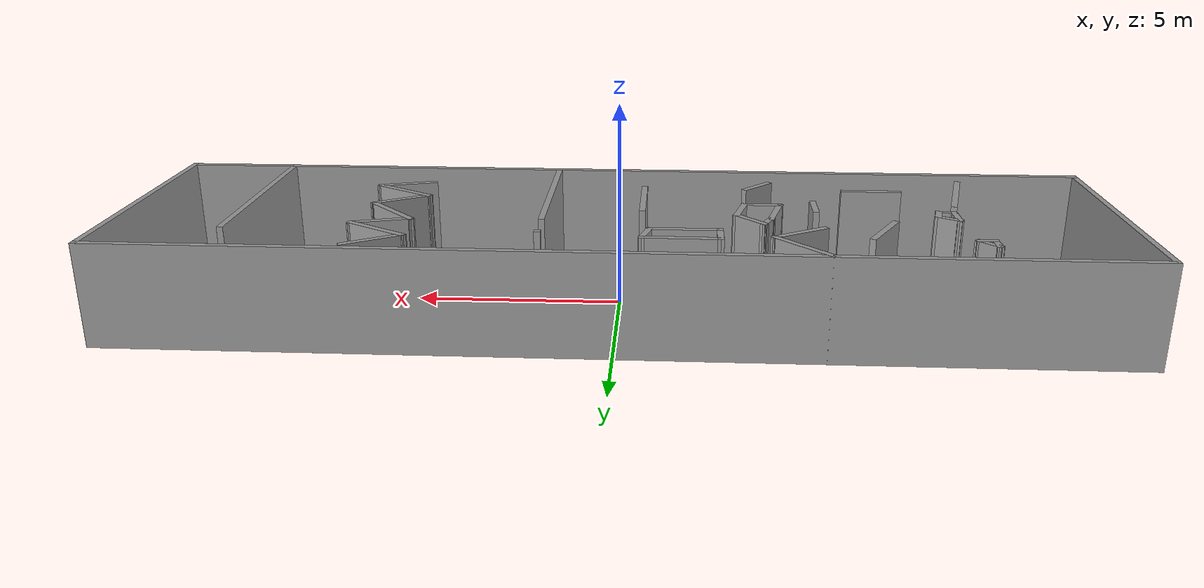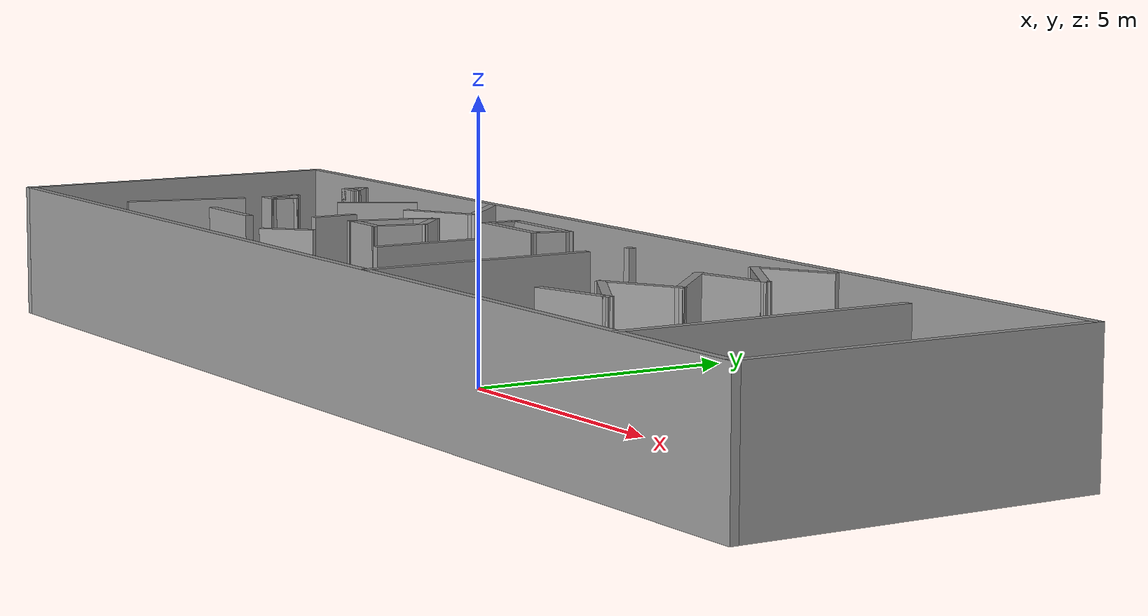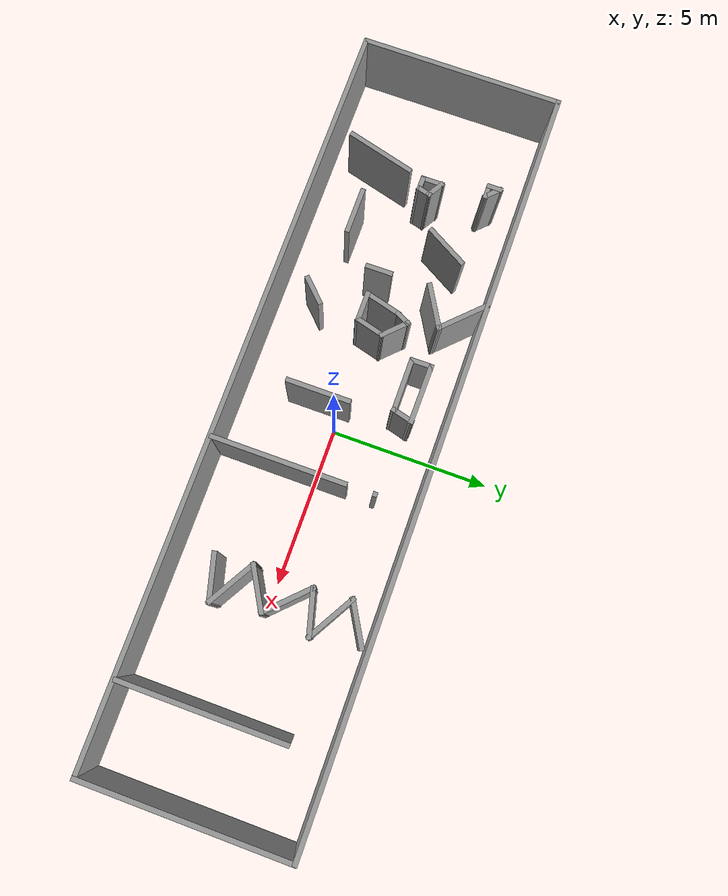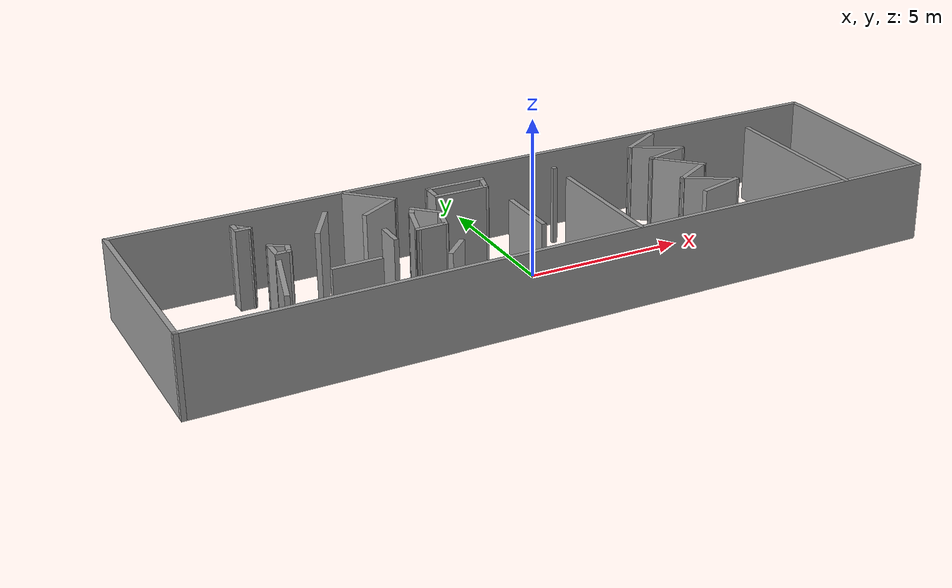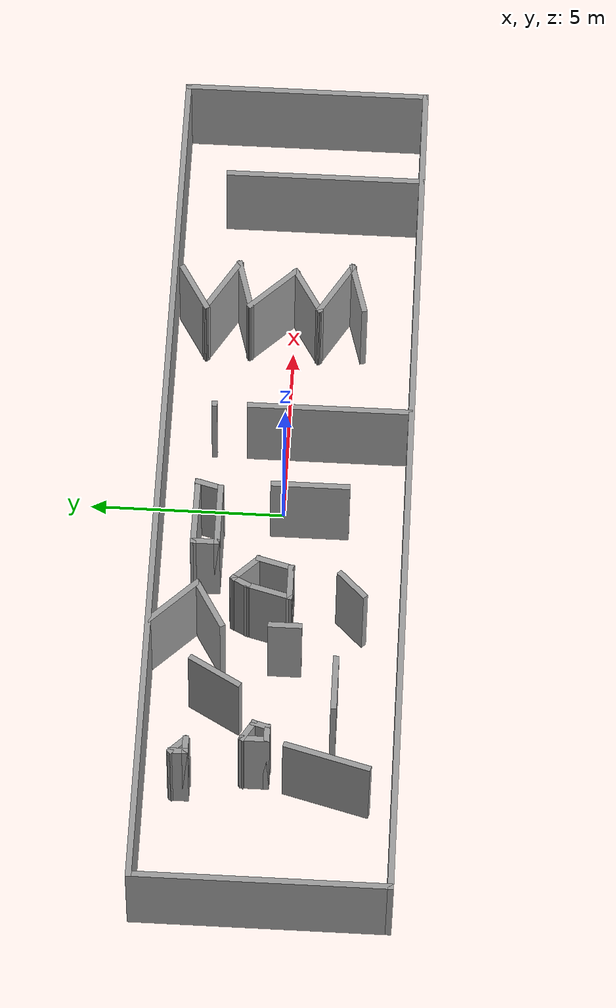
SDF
<?xml version='1.0'?>
<sdf version='1.6'>
  <model name='test2'>
    <link name='Wall_31'>
      <pose frame=''>0 3.17468 0 0 -0 0</pose>
      <self_collide>0</self_collide>
      <kinematic>0</kinematic>
      <visual name='Wall_31_Visual'>
        <pose frame=''>0 0 1.25 0 -0 0</pose>
        <geometry>
          <box>
            <size>23.75 0.15 2.5</size>
          </box>
        </geometry>
        <material>
          <script>
            <uri>file://media/materials/scripts/gazebo.material</uri>
            <name>Gazebo/Grey</name>
          </script>
          <ambient>1 1 1 1</ambient>
          <diffuse>0.7 0.7 0.7 1</diffuse>
          <specular>0.01 0.01 0.01 1</specular>
          <emissive>0 0 0 1</emissive>
        </material>
        <meta>
          <layer>0</layer>
        </meta>
        <transparency>0</transparency>
        <cast_shadows>1</cast_shadows>
      </visual>
      <collision name='Wall_31_Collision'>
        <laser_retro>0</laser_retro>
        <max_contacts>10</max_contacts>
        <pose frame=''>0 0 1.25 0 -0 0</pose>
        <geometry>
          <box>
            <size>23.75 0.15 2.5</size>
          </box>
        </geometry>
        <surface>
          <friction>
            <ode>
              <mu>1</mu>
              <mu2>1</mu2>
              <fdir1>0 0 0</fdir1>
              <slip1>0</slip1>
              <slip2>0</slip2>
            </ode>
            <torsional>
              <coefficient>1</coefficient>
              <patch_radius>0</patch_radius>
              <surface_radius>0</surface_radius>
              <use_patch_radius>1</use_patch_radius>
              <ode>
                <slip>0</slip>
              </ode>
            </torsional>
          </friction>
          <bounce>
            <restitution_coefficient>0</restitution_coefficient>
            <threshold>1e+06</threshold>
          </bounce>
          <contact>
            <collide_without_contact>0</collide_without_contact>
            <collide_without_contact_bitmask>1</collide_without_contact_bitmask>
            <collide_bitmask>1</collide_bitmask>
            <ode>
              <soft_cfm>0</soft_cfm>
              <soft_erp>0.2</soft_erp>
              <kp>1e+13</kp>
              <kd>1</kd>
              <max_vel>0.01</max_vel>
              <min_depth>0</min_depth>
            </ode>
            <bullet>
              <split_impulse>1</split_impulse>
              <split_impulse_penetration_threshold>-0.01</split_impulse_penetration_threshold>
              <soft_cfm>0</soft_cfm>
              <soft_erp>0.2</soft_erp>
              <kp>1e+13</kp>
              <kd>1</kd>
            </bullet>
          </contact>
        </surface>
      </collision>
    </link>
    <link name='Wall_32'>
      <pose frame=''>11.8 -0.000324 0 0 0 -1.5708</pose>
      <self_collide>0</self_collide>
      <kinematic>0</kinematic>
      <visual name='Wall_32_Visual'>
        <pose frame=''>0 0 1.25 0 -0 0</pose>
        <geometry>
          <box>
            <size>6.5 0.15 2.5</size>
          </box>
        </geometry>
        <material>
          <script>
            <uri>file://media/materials/scripts/gazebo.material</uri>
            <name>Gazebo/Grey</name>
          </script>
          <ambient>1 1 1 1</ambient>
          <diffuse>0.7 0.7 0.7 1</diffuse>
          <specular>0.01 0.01 0.01 1</specular>
          <emissive>0 0 0 1</emissive>
        </material>
        <meta>
          <layer>0</layer>
        </meta>
        <transparency>0</transparency>
        <cast_shadows>1</cast_shadows>
      </visual>
      <collision name='Wall_32_Collision'>
        <laser_retro>0</laser_retro>
        <max_contacts>10</max_contacts>
        <pose frame=''>0 0 1.25 0 -0 0</pose>
        <geometry>
          <box>
            <size>6.5 0.15 2.5</size>
          </box>
        </geometry>
        <surface>
          <friction>
            <ode>
              <mu>1</mu>
              <mu2>1</mu2>
              <fdir1>0 0 0</fdir1>
              <slip1>0</slip1>
              <slip2>0</slip2>
            </ode>
            <torsional>
              <coefficient>1</coefficient>
              <patch_radius>0</patch_radius>
              <surface_radius>0</surface_radius>
              <use_patch_radius>1</use_patch_radius>
              <ode>
                <slip>0</slip>
              </ode>
            </torsional>
          </friction>
          <bounce>
            <restitution_coefficient>0</restitution_coefficient>
            <threshold>1e+06</threshold>
          </bounce>
          <contact>
            <collide_without_contact>0</collide_without_contact>
            <collide_without_contact_bitmask>1</collide_without_contact_bitmask>
            <collide_bitmask>1</collide_bitmask>
            <ode>
              <soft_cfm>0</soft_cfm>
              <soft_erp>0.2</soft_erp>
              <kp>1e+13</kp>
              <kd>1</kd>
              <max_vel>0.01</max_vel>
              <min_depth>0</min_depth>
            </ode>
            <bullet>
              <split_impulse>1</split_impulse>
              <split_impulse_penetration_threshold>-0.01</split_impulse_penetration_threshold>
              <soft_cfm>0</soft_cfm>
              <soft_erp>0.2</soft_erp>
              <kp>1e+13</kp>
              <kd>1</kd>
            </bullet>
          </contact>
        </surface>
      </collision>
    </link>
    <link name='Wall_33'>
      <pose frame=''>0 -3.17532 0 0 -0 3.14159</pose>
      <self_collide>0</self_collide>
      <kinematic>0</kinematic>
      <visual name='Wall_33_Visual'>
        <pose frame=''>0 0 1.25 0 -0 0</pose>
        <geometry>
          <box>
            <size>23.75 0.15 2.5</size>
          </box>
        </geometry>
        <material>
          <script>
            <uri>file://media/materials/scripts/gazebo.material</uri>
            <name>Gazebo/Grey</name>
          </script>
          <ambient>1 1 1 1</ambient>
          <diffuse>0.7 0.7 0.7 1</diffuse>
          <specular>0.01 0.01 0.01 1</specular>
          <emissive>0 0 0 1</emissive>
        </material>
        <meta>
          <layer>0</layer>
        </meta>
        <transparency>0</transparency>
        <cast_shadows>1</cast_shadows>
      </visual>
      <collision name='Wall_33_Collision'>
        <laser_retro>0</laser_retro>
        <max_contacts>10</max_contacts>
        <pose frame=''>0 0 1.25 0 -0 0</pose>
        <geometry>
          <box>
            <size>23.75 0.15 2.5</size>
          </box>
        </geometry>
        <surface>
          <friction>
            <ode>
              <mu>1</mu>
              <mu2>1</mu2>
              <fdir1>0 0 0</fdir1>
              <slip1>0</slip1>
              <slip2>0</slip2>
            </ode>
            <torsional>
              <coefficient>1</coefficient>
              <patch_radius>0</patch_radius>
              <surface_radius>0</surface_radius>
              <use_patch_radius>1</use_patch_radius>
              <ode>
                <slip>0</slip>
              </ode>
            </torsional>
          </friction>
          <bounce>
            <restitution_coefficient>0</restitution_coefficient>
            <threshold>1e+06</threshold>
          </bounce>
          <contact>
            <collide_without_contact>0</collide_without_contact>
            <collide_without_contact_bitmask>1</collide_without_contact_bitmask>
            <collide_bitmask>1</collide_bitmask>
            <ode>
              <soft_cfm>0</soft_cfm>
              <soft_erp>0.2</soft_erp>
              <kp>1e+13</kp>
              <kd>1</kd>
              <max_vel>0.01</max_vel>
              <min_depth>0</min_depth>
            </ode>
            <bullet>
              <split_impulse>1</split_impulse>
              <split_impulse_penetration_threshold>-0.01</split_impulse_penetration_threshold>
              <soft_cfm>0</soft_cfm>
              <soft_erp>0.2</soft_erp>
              <kp>1e+13</kp>
              <kd>1</kd>
            </bullet>
          </contact>
        </surface>
      </collision>
    </link>
    <link name='Wall_34'>
      <pose frame=''>-11.8 -0.000324 0 0 -0 1.5708</pose>
      <self_collide>0</self_collide>
      <kinematic>0</kinematic>
      <visual name='Wall_34_Visual'>
        <pose frame=''>0 0 1.25 0 -0 0</pose>
        <geometry>
          <box>
            <size>6.5 0.15 2.5</size>
          </box>
        </geometry>
        <material>
          <script>
            <uri>file://media/materials/scripts/gazebo.material</uri>
            <name>Gazebo/Grey</name>
          </script>
          <ambient>1 1 1 1</ambient>
          <diffuse>0.7 0.7 0.7 1</diffuse>
          <specular>0.01 0.01 0.01 1</specular>
          <emissive>0 0 0 1</emissive>
        </material>
        <meta>
          <layer>0</layer>
        </meta>
        <transparency>0</transparency>
        <cast_shadows>1</cast_shadows>
      </visual>
      <collision name='Wall_34_Collision'>
        <laser_retro>0</laser_retro>
        <max_contacts>10</max_contacts>
        <pose frame=''>0 0 1.25 0 -0 0</pose>
        <geometry>
          <box>
            <size>6.5 0.15 2.5</size>
          </box>
        </geometry>
        <surface>
          <friction>
            <ode>
              <mu>1</mu>
              <mu2>1</mu2>
              <fdir1>0 0 0</fdir1>
              <slip1>0</slip1>
              <slip2>0</slip2>
            </ode>
            <torsional>
              <coefficient>1</coefficient>
              <patch_radius>0</patch_radius>
              <surface_radius>0</surface_radius>
              <use_patch_radius>1</use_patch_radius>
              <ode>
                <slip>0</slip>
              </ode>
            </torsional>
          </friction>
          <bounce>
            <restitution_coefficient>0</restitution_coefficient>
            <threshold>1e+06</threshold>
          </bounce>
          <contact>
            <collide_without_contact>0</collide_without_contact>
            <collide_without_contact_bitmask>1</collide_without_contact_bitmask>
            <collide_bitmask>1</collide_bitmask>
            <ode>
              <soft_cfm>0</soft_cfm>
              <soft_erp>0.2</soft_erp>
              <kp>1e+13</kp>
              <kd>1</kd>
              <max_vel>0.01</max_vel>
              <min_depth>0</min_depth>
            </ode>
            <bullet>
              <split_impulse>1</split_impulse>
              <split_impulse_penetration_threshold>-0.01</split_impulse_penetration_threshold>
              <soft_cfm>0</soft_cfm>
              <soft_erp>0.2</soft_erp>
              <kp>1e+13</kp>
              <kd>1</kd>
            </bullet>
          </contact>
        </surface>
      </collision>
    </link>
    <link name='Wall_36'>
      <pose frame=''>-8.37803 2.19361 0 0 0 -1.5708</pose>
      <self_collide>0</self_collide>
      <kinematic>0</kinematic>
      <visual name='Wall_36_Visual'>
        <pose frame=''>0 0 1.25 0 -0 0</pose>
        <geometry>
          <box>
            <size>0.5 0.15 2.5</size>
          </box>
        </geometry>
        <material>
          <script>
            <uri>file://media/materials/scripts/gazebo.material</uri>
            <name>Gazebo/Grey</name>
          </script>
          <ambient>1 1 1 1</ambient>
          <diffuse>0.7 0.7 0.7 1</diffuse>
          <specular>0.01 0.01 0.01 1</specular>
          <emissive>0 0 0 1</emissive>
        </material>
        <meta>
          <layer>0</layer>
        </meta>
        <transparency>0</transparency>
        <cast_shadows>1</cast_shadows>
      </visual>
      <collision name='Wall_36_Collision'>
        <laser_retro>0</laser_retro>
        <max_contacts>10</max_contacts>
        <pose frame=''>0 0 1.25 0 -0 0</pose>
        <geometry>
          <box>
            <size>0.5 0.15 2.5</size>
          </box>
        </geometry>
        <surface>
          <friction>
            <ode>
              <mu>1</mu>
              <mu2>1</mu2>
              <fdir1>0 0 0</fdir1>
              <slip1>0</slip1>
              <slip2>0</slip2>
            </ode>
            <torsional>
              <coefficient>1</coefficient>
              <patch_radius>0</patch_radius>
              <surface_radius>0</surface_radius>
              <use_patch_radius>1</use_patch_radius>
              <ode>
                <slip>0</slip>
              </ode>
            </torsional>
          </friction>
          <bounce>
            <restitution_coefficient>0</restitution_coefficient>
            <threshold>1e+06</threshold>
          </bounce>
          <contact>
            <collide_without_contact>0</collide_without_contact>
            <collide_without_contact_bitmask>1</collide_without_contact_bitmask>
            <collide_bitmask>1</collide_bitmask>
            <ode>
              <soft_cfm>0</soft_cfm>
              <soft_erp>0.2</soft_erp>
              <kp>1e+13</kp>
              <kd>1</kd>
              <max_vel>0.01</max_vel>
              <min_depth>0</min_depth>
            </ode>
            <bullet>
              <split_impulse>1</split_impulse>
              <split_impulse_penetration_threshold>-0.01</split_impulse_penetration_threshold>
              <soft_cfm>0</soft_cfm>
              <soft_erp>0.2</soft_erp>
              <kp>1e+13</kp>
              <kd>1</kd>
            </bullet>
          </contact>
        </surface>
      </collision>
    </link>
    <link name='Wall_38'>
      <pose frame=''>-8.20303 2.01861 0 0 -0 0</pose>
      <self_collide>0</self_collide>
      <kinematic>0</kinematic>
      <visual name='Wall_38_Visual'>
        <pose frame=''>0 0 1.25 0 -0 0</pose>
        <geometry>
          <box>
            <size>0.5 0.15 2.5</size>
          </box>
        </geometry>
        <material>
          <script>
            <uri>file://media/materials/scripts/gazebo.material</uri>
            <name>Gazebo/Grey</name>
          </script>
          <ambient>1 1 1 1</ambient>
          <diffuse>0.7 0.7 0.7 1</diffuse>
          <specular>0.01 0.01 0.01 1</specular>
          <emissive>0 0 0 1</emissive>
        </material>
        <meta>
          <layer>0</layer>
        </meta>
        <transparency>0</transparency>
        <cast_shadows>1</cast_shadows>
      </visual>
      <collision name='Wall_38_Collision'>
        <laser_retro>0</laser_retro>
        <max_contacts>10</max_contacts>
        <pose frame=''>0 0 1.25 0 -0 0</pose>
        <geometry>
          <box>
            <size>0.5 0.15 2.5</size>
          </box>
        </geometry>
        <surface>
          <friction>
            <ode>
              <mu>1</mu>
              <mu2>1</mu2>
              <fdir1>0 0 0</fdir1>
              <slip1>0</slip1>
              <slip2>0</slip2>
            </ode>
            <torsional>
              <coefficient>1</coefficient>
              <patch_radius>0</patch_radius>
              <surface_radius>0</surface_radius>
              <use_patch_radius>1</use_patch_radius>
              <ode>
                <slip>0</slip>
              </ode>
            </torsional>
          </friction>
          <bounce>
            <restitution_coefficient>0</restitution_coefficient>
            <threshold>1e+06</threshold>
          </bounce>
          <contact>
            <collide_without_contact>0</collide_without_contact>
            <collide_without_contact_bitmask>1</collide_without_contact_bitmask>
            <collide_bitmask>1</collide_bitmask>
            <ode>
              <soft_cfm>0</soft_cfm>
              <soft_erp>0.2</soft_erp>
              <kp>1e+13</kp>
              <kd>1</kd>
              <max_vel>0.01</max_vel>
              <min_depth>0</min_depth>
            </ode>
            <bullet>
              <split_impulse>1</split_impulse>
              <split_impulse_penetration_threshold>-0.01</split_impulse_penetration_threshold>
              <soft_cfm>0</soft_cfm>
              <soft_erp>0.2</soft_erp>
              <kp>1e+13</kp>
              <kd>1</kd>
            </bullet>
          </contact>
        </surface>
      </collision>
    </link>
    <link name='Wall_39'>
      <pose frame=''>-8.20303 2.19361 0 0 -0 2.35619</pose>
      <self_collide>0</self_collide>
      <kinematic>0</kinematic>
      <visual name='Wall_39_Visual'>
        <pose frame=''>0 0 1.25 0 -0 0</pose>
        <geometry>
          <box>
            <size>0.644975 0.15 2.5</size>
          </box>
        </geometry>
        <material>
          <script>
            <uri>file://media/materials/scripts/gazebo.material</uri>
            <name>Gazebo/Grey</name>
          </script>
          <ambient>1 1 1 1</ambient>
          <diffuse>0.7 0.7 0.7 1</diffuse>
          <specular>0.01 0.01 0.01 1</specular>
          <emissive>0 0 0 1</emissive>
        </material>
        <meta>
          <layer>0</layer>
        </meta>
        <transparency>0</transparency>
        <cast_shadows>1</cast_shadows>
      </visual>
      <collision name='Wall_39_Collision'>
        <laser_retro>0</laser_retro>
        <max_contacts>10</max_contacts>
        <pose frame=''>0 0 1.25 0 -0 0</pose>
        <geometry>
          <box>
            <size>0.644975 0.15 2.5</size>
          </box>
        </geometry>
        <surface>
          <friction>
            <ode>
              <mu>1</mu>
              <mu2>1</mu2>
              <fdir1>0 0 0</fdir1>
              <slip1>0</slip1>
              <slip2>0</slip2>
            </ode>
            <torsional>
              <coefficient>1</coefficient>
              <patch_radius>0</patch_radius>
              <surface_radius>0</surface_radius>
              <use_patch_radius>1</use_patch_radius>
              <ode>
                <slip>0</slip>
              </ode>
            </torsional>
          </friction>
          <bounce>
            <restitution_coefficient>0</restitution_coefficient>
            <threshold>1e+06</threshold>
          </bounce>
          <contact>
            <collide_without_contact>0</collide_without_contact>
            <collide_without_contact_bitmask>1</collide_without_contact_bitmask>
            <collide_bitmask>1</collide_bitmask>
            <ode>
              <soft_cfm>0</soft_cfm>
              <soft_erp>0.2</soft_erp>
              <kp>1e+13</kp>
              <kd>1</kd>
              <max_vel>0.01</max_vel>
              <min_depth>0</min_depth>
            </ode>
            <bullet>
              <split_impulse>1</split_impulse>
              <split_impulse_penetration_threshold>-0.01</split_impulse_penetration_threshold>
              <soft_cfm>0</soft_cfm>
              <soft_erp>0.2</soft_erp>
              <kp>1e+13</kp>
              <kd>1</kd>
            </bullet>
          </contact>
        </surface>
      </collision>
    </link>
    <link name='Wall_41'>
      <pose frame=''>-7.93698 0.334815 0 0 0 -1.5708</pose>
      <self_collide>0</self_collide>
      <kinematic>0</kinematic>
      <visual name='Wall_41_Visual'>
        <pose frame=''>0 0 1.25 0 -0 0</pose>
        <geometry>
          <box>
            <size>0.75 0.15 2.5</size>
          </box>
        </geometry>
        <material>
          <script>
            <uri>file://media/materials/scripts/gazebo.material</uri>
            <name>Gazebo/Grey</name>
          </script>
          <ambient>1 1 1 1</ambient>
          <diffuse>0.7 0.7 0.7 1</diffuse>
          <specular>0.01 0.01 0.01 1</specular>
          <emissive>0 0 0 1</emissive>
        </material>
        <meta>
          <layer>0</layer>
        </meta>
        <transparency>0</transparency>
        <cast_shadows>1</cast_shadows>
      </visual>
      <collision name='Wall_41_Collision'>
        <laser_retro>0</laser_retro>
        <max_contacts>10</max_contacts>
        <pose frame=''>0 0 1.25 0 -0 0</pose>
        <geometry>
          <box>
            <size>0.75 0.15 2.5</size>
          </box>
        </geometry>
        <surface>
          <friction>
            <ode>
              <mu>1</mu>
              <mu2>1</mu2>
              <fdir1>0 0 0</fdir1>
              <slip1>0</slip1>
              <slip2>0</slip2>
            </ode>
            <torsional>
              <coefficient>1</coefficient>
              <patch_radius>0</patch_radius>
              <surface_radius>0</surface_radius>
              <use_patch_radius>1</use_patch_radius>
              <ode>
                <slip>0</slip>
              </ode>
            </torsional>
          </friction>
          <bounce>
            <restitution_coefficient>0</restitution_coefficient>
            <threshold>1e+06</threshold>
          </bounce>
          <contact>
            <collide_without_contact>0</collide_without_contact>
            <collide_without_contact_bitmask>1</collide_without_contact_bitmask>
            <collide_bitmask>1</collide_bitmask>
            <ode>
              <soft_cfm>0</soft_cfm>
              <soft_erp>0.2</soft_erp>
              <kp>1e+13</kp>
              <kd>1</kd>
              <max_vel>0.01</max_vel>
              <min_depth>0</min_depth>
            </ode>
            <bullet>
              <split_impulse>1</split_impulse>
              <split_impulse_penetration_threshold>-0.01</split_impulse_penetration_threshold>
              <soft_cfm>0</soft_cfm>
              <soft_erp>0.2</soft_erp>
              <kp>1e+13</kp>
              <kd>1</kd>
            </bullet>
          </contact>
        </surface>
      </collision>
    </link>
    <link name='Wall_42'>
      <pose frame=''>-7.76198 0.034815 0 0 -0 0</pose>
      <self_collide>0</self_collide>
      <kinematic>0</kinematic>
      <visual name='Wall_42_Visual'>
        <pose frame=''>0 0 1.25 0 -0 0</pose>
        <geometry>
          <box>
            <size>0.5 0.15 2.5</size>
          </box>
        </geometry>
        <material>
          <script>
            <uri>file://media/materials/scripts/gazebo.material</uri>
            <name>Gazebo/Grey</name>
          </script>
          <ambient>1 1 1 1</ambient>
          <diffuse>0.7 0.7 0.7 1</diffuse>
          <specular>0.01 0.01 0.01 1</specular>
          <emissive>0 0 0 1</emissive>
        </material>
        <meta>
          <layer>0</layer>
        </meta>
        <transparency>0</transparency>
        <cast_shadows>1</cast_shadows>
      </visual>
      <collision name='Wall_42_Collision'>
        <laser_retro>0</laser_retro>
        <max_contacts>10</max_contacts>
        <pose frame=''>0 0 1.25 0 -0 0</pose>
        <geometry>
          <box>
            <size>0.5 0.15 2.5</size>
          </box>
        </geometry>
        <surface>
          <friction>
            <ode>
              <mu>1</mu>
              <mu2>1</mu2>
              <fdir1>0 0 0</fdir1>
              <slip1>0</slip1>
              <slip2>0</slip2>
            </ode>
            <torsional>
              <coefficient>1</coefficient>
              <patch_radius>0</patch_radius>
              <surface_radius>0</surface_radius>
              <use_patch_radius>1</use_patch_radius>
              <ode>
                <slip>0</slip>
              </ode>
            </torsional>
          </friction>
          <bounce>
            <restitution_coefficient>0</restitution_coefficient>
            <threshold>1e+06</threshold>
          </bounce>
          <contact>
            <collide_without_contact>0</collide_without_contact>
            <collide_without_contact_bitmask>1</collide_without_contact_bitmask>
            <collide_bitmask>1</collide_bitmask>
            <ode>
              <soft_cfm>0</soft_cfm>
              <soft_erp>0.2</soft_erp>
              <kp>1e+13</kp>
              <kd>1</kd>
              <max_vel>0.01</max_vel>
              <min_depth>0</min_depth>
            </ode>
            <bullet>
              <split_impulse>1</split_impulse>
              <split_impulse_penetration_threshold>-0.01</split_impulse_penetration_threshold>
              <soft_cfm>0</soft_cfm>
              <soft_erp>0.2</soft_erp>
              <kp>1e+13</kp>
              <kd>1</kd>
            </bullet>
          </contact>
        </surface>
      </collision>
    </link>
    <link name='Wall_43'>
      <pose frame=''>-7.54168 0.203852 0 0 -0 1.309</pose>
      <self_collide>0</self_collide>
      <kinematic>0</kinematic>
      <visual name='Wall_43_Visual'>
        <pose frame=''>0 0 1.25 0 -0 0</pose>
        <geometry>
          <box>
            <size>0.5 0.15 2.5</size>
          </box>
        </geometry>
        <material>
          <script>
            <uri>file://media/materials/scripts/gazebo.material</uri>
            <name>Gazebo/Grey</name>
          </script>
          <ambient>1 1 1 1</ambient>
          <diffuse>0.7 0.7 0.7 1</diffuse>
          <specular>0.01 0.01 0.01 1</specular>
          <emissive>0 0 0 1</emissive>
        </material>
        <meta>
          <layer>0</layer>
        </meta>
        <transparency>0</transparency>
        <cast_shadows>1</cast_shadows>
      </visual>
      <collision name='Wall_43_Collision'>
        <laser_retro>0</laser_retro>
        <max_contacts>10</max_contacts>
        <pose frame=''>0 0 1.25 0 -0 0</pose>
        <geometry>
          <box>
            <size>0.5 0.15 2.5</size>
          </box>
        </geometry>
        <surface>
          <friction>
            <ode>
              <mu>1</mu>
              <mu2>1</mu2>
              <fdir1>0 0 0</fdir1>
              <slip1>0</slip1>
              <slip2>0</slip2>
            </ode>
            <torsional>
              <coefficient>1</coefficient>
              <patch_radius>0</patch_radius>
              <surface_radius>0</surface_radius>
              <use_patch_radius>1</use_patch_radius>
              <ode>
                <slip>0</slip>
              </ode>
            </torsional>
          </friction>
          <bounce>
            <restitution_coefficient>0</restitution_coefficient>
            <threshold>1e+06</threshold>
          </bounce>
          <contact>
            <collide_without_contact>0</collide_without_contact>
            <collide_without_contact_bitmask>1</collide_without_contact_bitmask>
            <collide_bitmask>1</collide_bitmask>
            <ode>
              <soft_cfm>0</soft_cfm>
              <soft_erp>0.2</soft_erp>
              <kp>1e+13</kp>
              <kd>1</kd>
              <max_vel>0.01</max_vel>
              <min_depth>0</min_depth>
            </ode>
            <bullet>
              <split_impulse>1</split_impulse>
              <split_impulse_penetration_threshold>-0.01</split_impulse_penetration_threshold>
              <soft_cfm>0</soft_cfm>
              <soft_erp>0.2</soft_erp>
              <kp>1e+13</kp>
              <kd>1</kd>
            </bullet>
          </contact>
        </surface>
      </collision>
    </link>
    <link name='Wall_44'>
      <pose frame=''>-7.71668 0.503852 0 0 -0 2.60523</pose>
      <self_collide>0</self_collide>
      <kinematic>0</kinematic>
      <visual name='Wall_44_Visual'>
        <pose frame=''>0 0 1.25 0 -0 0</pose>
        <geometry>
          <box>
            <size>0.662564 0.15 2.5</size>
          </box>
        </geometry>
        <material>
          <script>
            <uri>file://media/materials/scripts/gazebo.material</uri>
            <name>Gazebo/Grey</name>
          </script>
          <ambient>1 1 1 1</ambient>
          <diffuse>0.7 0.7 0.7 1</diffuse>
          <specular>0.01 0.01 0.01 1</specular>
          <emissive>0 0 0 1</emissive>
        </material>
        <meta>
          <layer>0</layer>
        </meta>
        <transparency>0</transparency>
        <cast_shadows>1</cast_shadows>
      </visual>
      <collision name='Wall_44_Collision'>
        <laser_retro>0</laser_retro>
        <max_contacts>10</max_contacts>
        <pose frame=''>0 0 1.25 0 -0 0</pose>
        <geometry>
          <box>
            <size>0.662564 0.15 2.5</size>
          </box>
        </geometry>
        <surface>
          <friction>
            <ode>
              <mu>1</mu>
              <mu2>1</mu2>
              <fdir1>0 0 0</fdir1>
              <slip1>0</slip1>
              <slip2>0</slip2>
            </ode>
            <torsional>
              <coefficient>1</coefficient>
              <patch_radius>0</patch_radius>
              <surface_radius>0</surface_radius>
              <use_patch_radius>1</use_patch_radius>
              <ode>
                <slip>0</slip>
              </ode>
            </torsional>
          </friction>
          <bounce>
            <restitution_coefficient>0</restitution_coefficient>
            <threshold>1e+06</threshold>
          </bounce>
          <contact>
            <collide_without_contact>0</collide_without_contact>
            <collide_without_contact_bitmask>1</collide_without_contact_bitmask>
            <collide_bitmask>1</collide_bitmask>
            <ode>
              <soft_cfm>0</soft_cfm>
              <soft_erp>0.2</soft_erp>
              <kp>1e+13</kp>
              <kd>1</kd>
              <max_vel>0.01</max_vel>
              <min_depth>0</min_depth>
            </ode>
            <bullet>
              <split_impulse>1</split_impulse>
              <split_impulse_penetration_threshold>-0.01</split_impulse_penetration_threshold>
              <soft_cfm>0</soft_cfm>
              <soft_erp>0.2</soft_erp>
              <kp>1e+13</kp>
              <kd>1</kd>
            </bullet>
          </contact>
        </surface>
      </collision>
    </link>
    <link name='Wall_46'>
      <pose frame=''>-8.33041 -1.47444 0 0 0 -1.8326</pose>
      <self_collide>0</self_collide>
      <kinematic>0</kinematic>
      <visual name='Wall_46_Visual'>
        <pose frame=''>0 0 1.25 0 -0 0</pose>
        <geometry>
          <box>
            <size>2.25 0.15 2.5</size>
          </box>
        </geometry>
        <material>
          <script>
            <uri>file://media/materials/scripts/gazebo.material</uri>
            <name>Gazebo/Grey</name>
          </script>
          <ambient>1 1 1 1</ambient>
          <diffuse>0.7 0.7 0.7 1</diffuse>
          <specular>0.01 0.01 0.01 1</specular>
          <emissive>0 0 0 1</emissive>
        </material>
        <meta>
          <layer>0</layer>
        </meta>
        <transparency>0</transparency>
        <cast_shadows>1</cast_shadows>
      </visual>
      <collision name='Wall_46_Collision'>
        <laser_retro>0</laser_retro>
        <max_contacts>10</max_contacts>
        <pose frame=''>0 0 1.25 0 -0 0</pose>
        <geometry>
          <box>
            <size>2.25 0.15 2.5</size>
          </box>
        </geometry>
        <surface>
          <friction>
            <ode>
              <mu>1</mu>
              <mu2>1</mu2>
              <fdir1>0 0 0</fdir1>
              <slip1>0</slip1>
              <slip2>0</slip2>
            </ode>
            <torsional>
              <coefficient>1</coefficient>
              <patch_radius>0</patch_radius>
              <surface_radius>0</surface_radius>
              <use_patch_radius>1</use_patch_radius>
              <ode>
                <slip>0</slip>
              </ode>
            </torsional>
          </friction>
          <bounce>
            <restitution_coefficient>0</restitution_coefficient>
            <threshold>1e+06</threshold>
          </bounce>
          <contact>
            <collide_without_contact>0</collide_without_contact>
            <collide_without_contact_bitmask>1</collide_without_contact_bitmask>
            <collide_bitmask>1</collide_bitmask>
            <ode>
              <soft_cfm>0</soft_cfm>
              <soft_erp>0.2</soft_erp>
              <kp>1e+13</kp>
              <kd>1</kd>
              <max_vel>0.01</max_vel>
              <min_depth>0</min_depth>
            </ode>
            <bullet>
              <split_impulse>1</split_impulse>
              <split_impulse_penetration_threshold>-0.01</split_impulse_penetration_threshold>
              <soft_cfm>0</soft_cfm>
              <soft_erp>0.2</soft_erp>
              <kp>1e+13</kp>
              <kd>1</kd>
            </bullet>
          </contact>
        </surface>
      </collision>
    </link>
    <link name='Wall_48'>
      <pose frame=''>-6.0786 1.4171 0 0 -0 1.0472</pose>
      <self_collide>0</self_collide>
      <kinematic>0</kinematic>
      <visual name='Wall_48_Visual'>
        <pose frame=''>0 0 1.25 0 -0 0</pose>
        <geometry>
          <box>
            <size>1.5 0.15 2.5</size>
          </box>
        </geometry>
        <material>
          <script>
            <uri>file://media/materials/scripts/gazebo.material</uri>
            <name>Gazebo/Grey</name>
          </script>
          <ambient>1 1 1 1</ambient>
          <diffuse>0.7 0.7 0.7 1</diffuse>
          <specular>0.01 0.01 0.01 1</specular>
          <emissive>0 0 0 1</emissive>
        </material>
        <meta>
          <layer>0</layer>
        </meta>
        <transparency>0</transparency>
        <cast_shadows>1</cast_shadows>
      </visual>
      <collision name='Wall_48_Collision'>
        <laser_retro>0</laser_retro>
        <max_contacts>10</max_contacts>
        <pose frame=''>0 0 1.25 0 -0 0</pose>
        <geometry>
          <box>
            <size>1.5 0.15 2.5</size>
          </box>
        </geometry>
        <surface>
          <friction>
            <ode>
              <mu>1</mu>
              <mu2>1</mu2>
              <fdir1>0 0 0</fdir1>
              <slip1>0</slip1>
              <slip2>0</slip2>
            </ode>
            <torsional>
              <coefficient>1</coefficient>
              <patch_radius>0</patch_radius>
              <surface_radius>0</surface_radius>
              <use_patch_radius>1</use_patch_radius>
              <ode>
                <slip>0</slip>
              </ode>
            </torsional>
          </friction>
          <bounce>
            <restitution_coefficient>0</restitution_coefficient>
            <threshold>1e+06</threshold>
          </bounce>
          <contact>
            <collide_without_contact>0</collide_without_contact>
            <collide_without_contact_bitmask>1</collide_without_contact_bitmask>
            <collide_bitmask>1</collide_bitmask>
            <ode>
              <soft_cfm>0</soft_cfm>
              <soft_erp>0.2</soft_erp>
              <kp>1e+13</kp>
              <kd>1</kd>
              <max_vel>0.01</max_vel>
              <min_depth>0</min_depth>
            </ode>
            <bullet>
              <split_impulse>1</split_impulse>
              <split_impulse_penetration_threshold>-0.01</split_impulse_penetration_threshold>
              <soft_cfm>0</soft_cfm>
              <soft_erp>0.2</soft_erp>
              <kp>1e+13</kp>
              <kd>1</kd>
            </bullet>
          </contact>
        </surface>
      </collision>
    </link>
    <link name='Wall_50'>
      <pose frame=''>-4.13183 2.57857 0 0 0 -0.785398</pose>
      <self_collide>0</self_collide>
      <kinematic>0</kinematic>
      <visual name='Wall_50_Visual'>
        <pose frame=''>0 0 1.25 0 -0 0</pose>
        <geometry>
          <box>
            <size>1.75 0.15 2.5</size>
          </box>
        </geometry>
        <material>
          <script>
            <uri>file://media/materials/scripts/gazebo.material</uri>
            <name>Gazebo/Grey</name>
          </script>
          <ambient>1 1 1 1</ambient>
          <diffuse>0.7 0.7 0.7 1</diffuse>
          <specular>0.01 0.01 0.01 1</specular>
          <emissive>0 0 0 1</emissive>
        </material>
        <meta>
          <layer>0</layer>
        </meta>
        <transparency>0</transparency>
        <cast_shadows>1</cast_shadows>
      </visual>
      <collision name='Wall_50_Collision'>
        <laser_retro>0</laser_retro>
        <max_contacts>10</max_contacts>
        <pose frame=''>0 0 1.25 0 -0 0</pose>
        <geometry>
          <box>
            <size>1.75 0.15 2.5</size>
          </box>
        </geometry>
        <surface>
          <friction>
            <ode>
              <mu>1</mu>
              <mu2>1</mu2>
              <fdir1>0 0 0</fdir1>
              <slip1>0</slip1>
              <slip2>0</slip2>
            </ode>
            <torsional>
              <coefficient>1</coefficient>
              <patch_radius>0</patch_radius>
              <surface_radius>0</surface_radius>
              <use_patch_radius>1</use_patch_radius>
              <ode>
                <slip>0</slip>
              </ode>
            </torsional>
          </friction>
          <bounce>
            <restitution_coefficient>0</restitution_coefficient>
            <threshold>1e+06</threshold>
          </bounce>
          <contact>
            <collide_without_contact>0</collide_without_contact>
            <collide_without_contact_bitmask>1</collide_without_contact_bitmask>
            <collide_bitmask>1</collide_bitmask>
            <ode>
              <soft_cfm>0</soft_cfm>
              <soft_erp>0.2</soft_erp>
              <kp>1e+13</kp>
              <kd>1</kd>
              <max_vel>0.01</max_vel>
              <min_depth>0</min_depth>
            </ode>
            <bullet>
              <split_impulse>1</split_impulse>
              <split_impulse_penetration_threshold>-0.01</split_impulse_penetration_threshold>
              <soft_cfm>0</soft_cfm>
              <soft_erp>0.2</soft_erp>
              <kp>1e+13</kp>
              <kd>1</kd>
            </bullet>
          </contact>
        </surface>
      </collision>
    </link>
    <link name='Wall_51'>
      <pose frame=''>-4.15071 1.67539 0 0 0 -2.61799</pose>
      <self_collide>0</self_collide>
      <kinematic>0</kinematic>
      <visual name='Wall_51_Visual'>
        <pose frame=''>0 0 1.25 0 -0 0</pose>
        <geometry>
          <box>
            <size>1.5 0.15 2.5</size>
          </box>
        </geometry>
        <material>
          <script>
            <uri>file://media/materials/scripts/gazebo.material</uri>
            <name>Gazebo/Grey</name>
          </script>
          <ambient>1 1 1 1</ambient>
          <diffuse>0.7 0.7 0.7 1</diffuse>
          <specular>0.01 0.01 0.01 1</specular>
          <emissive>0 0 0 1</emissive>
        </material>
        <meta>
          <layer>0</layer>
        </meta>
        <transparency>0</transparency>
        <cast_shadows>1</cast_shadows>
      </visual>
      <collision name='Wall_51_Collision'>
        <laser_retro>0</laser_retro>
        <max_contacts>10</max_contacts>
        <pose frame=''>0 0 1.25 0 -0 0</pose>
        <geometry>
          <box>
            <size>1.5 0.15 2.5</size>
          </box>
        </geometry>
        <surface>
          <friction>
            <ode>
              <mu>1</mu>
              <mu2>1</mu2>
              <fdir1>0 0 0</fdir1>
              <slip1>0</slip1>
              <slip2>0</slip2>
            </ode>
            <torsional>
              <coefficient>1</coefficient>
              <patch_radius>0</patch_radius>
              <surface_radius>0</surface_radius>
              <use_patch_radius>1</use_patch_radius>
              <ode>
                <slip>0</slip>
              </ode>
            </torsional>
          </friction>
          <bounce>
            <restitution_coefficient>0</restitution_coefficient>
            <threshold>1e+06</threshold>
          </bounce>
          <contact>
            <collide_without_contact>0</collide_without_contact>
            <collide_without_contact_bitmask>1</collide_without_contact_bitmask>
            <collide_bitmask>1</collide_bitmask>
            <ode>
              <soft_cfm>0</soft_cfm>
              <soft_erp>0.2</soft_erp>
              <kp>1e+13</kp>
              <kd>1</kd>
              <max_vel>0.01</max_vel>
              <min_depth>0</min_depth>
            </ode>
            <bullet>
              <split_impulse>1</split_impulse>
              <split_impulse_penetration_threshold>-0.01</split_impulse_penetration_threshold>
              <soft_cfm>0</soft_cfm>
              <soft_erp>0.2</soft_erp>
              <kp>1e+13</kp>
              <kd>1</kd>
            </bullet>
          </contact>
        </surface>
      </collision>
    </link>
    <link name='Wall_53'>
      <pose frame=''>-4.68231 -0.253108 0 0 0 -1.5708</pose>
      <self_collide>0</self_collide>
      <kinematic>0</kinematic>
      <inertial>
        <inertia>
          <ixx>nan</ixx>
          <ixy>0</ixy>
          <ixz>0</ixz>
          <iyy>nan</iyy>
          <iyz>0</iyz>
          <izz>nan</izz>
        </inertia>
        <mass>0</mass>
        <pose frame=''>0 0 0 0 -0 0</pose>
      </inertial>
      <visual name='Wall_53_Visual'>
        <pose frame=''>0 0 1.25 0 -0 0</pose>
        <geometry>
          <box>
            <size>0.856959 0.15 2.5</size>
          </box>
        </geometry>
        <material>
          <script>
            <uri>file://media/materials/scripts/gazebo.material</uri>
            <name>Gazebo/Grey</name>
          </script>
          <ambient>1 1 1 1</ambient>
          <diffuse>0.7 0.7 0.7 1</diffuse>
          <specular>0.01 0.01 0.01 1</specular>
          <emissive>0 0 0 1</emissive>
        </material>
        <meta>
          <layer>0</layer>
        </meta>
        <transparency>0</transparency>
        <cast_shadows>1</cast_shadows>
      </visual>
      <collision name='Wall_53_Collision'>
        <laser_retro>0</laser_retro>
        <max_contacts>10</max_contacts>
        <pose frame=''>0 0 1.25 0 -0 0</pose>
        <geometry>
          <box>
            <size>0.856959 0.15 2.5</size>
          </box>
        </geometry>
        <surface>
          <friction>
            <ode>
              <mu>1</mu>
              <mu2>1</mu2>
              <fdir1>0 0 0</fdir1>
              <slip1>0</slip1>
              <slip2>0</slip2>
            </ode>
            <torsional>
              <coefficient>1</coefficient>
              <patch_radius>0</patch_radius>
              <surface_radius>0</surface_radius>
              <use_patch_radius>1</use_patch_radius>
              <ode>
                <slip>0</slip>
              </ode>
            </torsional>
          </friction>
          <bounce>
            <restitution_coefficient>0</restitution_coefficient>
            <threshold>1e+06</threshold>
          </bounce>
          <contact>
            <collide_without_contact>0</collide_without_contact>
            <collide_without_contact_bitmask>1</collide_without_contact_bitmask>
            <collide_bitmask>1</collide_bitmask>
            <ode>
              <soft_cfm>0</soft_cfm>
              <soft_erp>0.2</soft_erp>
              <kp>1e+13</kp>
              <kd>1</kd>
              <max_vel>0.01</max_vel>
              <min_depth>0</min_depth>
            </ode>
            <bullet>
              <split_impulse>1</split_impulse>
              <split_impulse_penetration_threshold>-0.01</split_impulse_penetration_threshold>
              <soft_cfm>0</soft_cfm>
              <soft_erp>0.2</soft_erp>
              <kp>1e+13</kp>
              <kd>1</kd>
            </bullet>
          </contact>
        </surface>
      </collision>
    </link>
    <link name='Wall_55'>
      <pose frame=''>-6.24299 -1.57045 0 0 -0 0</pose>
      <self_collide>0</self_collide>
      <kinematic>0</kinematic>
      <visual name='Wall_55_Visual'>
        <pose frame=''>0 0 1.25 0 -0 0</pose>
        <geometry>
          <box>
            <size>1.5 0.15 2.5</size>
          </box>
        </geometry>
        <material>
          <script>
            <uri>file://media/materials/scripts/gazebo.material</uri>
            <name>Gazebo/Grey</name>
          </script>
          <ambient>1 1 1 1</ambient>
          <diffuse>0.7 0.7 0.7 1</diffuse>
          <specular>0.01 0.01 0.01 1</specular>
          <emissive>0 0 0 1</emissive>
        </material>
        <meta>
          <layer>0</layer>
        </meta>
        <transparency>0</transparency>
        <cast_shadows>1</cast_shadows>
      </visual>
      <collision name='Wall_55_Collision'>
        <laser_retro>0</laser_retro>
        <max_contacts>10</max_contacts>
        <pose frame=''>0 0 1.25 0 -0 0</pose>
        <geometry>
          <box>
            <size>1.5 0.15 2.5</size>
          </box>
        </geometry>
        <surface>
          <friction>
            <ode>
              <mu>1</mu>
              <mu2>1</mu2>
              <fdir1>0 0 0</fdir1>
              <slip1>0</slip1>
              <slip2>0</slip2>
            </ode>
            <torsional>
              <coefficient>1</coefficient>
              <patch_radius>0</patch_radius>
              <surface_radius>0</surface_radius>
              <use_patch_radius>1</use_patch_radius>
              <ode>
                <slip>0</slip>
              </ode>
            </torsional>
          </friction>
          <bounce>
            <restitution_coefficient>0</restitution_coefficient>
            <threshold>1e+06</threshold>
          </bounce>
          <contact>
            <collide_without_contact>0</collide_without_contact>
            <collide_without_contact_bitmask>1</collide_without_contact_bitmask>
            <collide_bitmask>1</collide_bitmask>
            <ode>
              <soft_cfm>0</soft_cfm>
              <soft_erp>0.2</soft_erp>
              <kp>1e+13</kp>
              <kd>1</kd>
              <max_vel>0.01</max_vel>
              <min_depth>0</min_depth>
            </ode>
            <bullet>
              <split_impulse>1</split_impulse>
              <split_impulse_penetration_threshold>-0.01</split_impulse_penetration_threshold>
              <soft_cfm>0</soft_cfm>
              <soft_erp>0.2</soft_erp>
              <kp>1e+13</kp>
              <kd>1</kd>
            </bullet>
          </contact>
        </surface>
      </collision>
    </link>
    <link name='Wall_57'>
      <pose frame=''>-3.4105 -1.87878 0 0 -0 0.785398</pose>
      <self_collide>0</self_collide>
      <kinematic>0</kinematic>
      <inertial>
        <inertia>
          <ixx>nan</ixx>
          <ixy>0</ixy>
          <ixz>0</ixz>
          <iyy>nan</iyy>
          <iyz>0</iyz>
          <izz>nan</izz>
        </inertia>
        <mass>0</mass>
        <pose frame=''>0 0 0 0 -0 0</pose>
      </inertial>
      <visual name='Wall_57_Visual'>
        <pose frame=''>0 0 1.25 0 -0 0</pose>
        <geometry>
          <box>
            <size>0.984753 0.15 2.5</size>
          </box>
        </geometry>
        <material>
          <script>
            <uri>file://media/materials/scripts/gazebo.material</uri>
            <name>Gazebo/Grey</name>
          </script>
          <ambient>1 1 1 1</ambient>
          <diffuse>0.7 0.7 0.7 1</diffuse>
          <specular>0.01 0.01 0.01 1</specular>
          <emissive>0 0 0 1</emissive>
        </material>
        <meta>
          <layer>0</layer>
        </meta>
        <transparency>0</transparency>
        <cast_shadows>1</cast_shadows>
      </visual>
      <collision name='Wall_57_Collision'>
        <laser_retro>0</laser_retro>
        <max_contacts>10</max_contacts>
        <pose frame=''>0 0 1.25 0 -0 0</pose>
        <geometry>
          <box>
            <size>0.984753 0.15 2.5</size>
          </box>
        </geometry>
        <surface>
          <friction>
            <ode>
              <mu>1</mu>
              <mu2>1</mu2>
              <fdir1>0 0 0</fdir1>
              <slip1>0</slip1>
              <slip2>0</slip2>
            </ode>
            <torsional>
              <coefficient>1</coefficient>
              <patch_radius>0</patch_radius>
              <surface_radius>0</surface_radius>
              <use_patch_radius>1</use_patch_radius>
              <ode>
                <slip>0</slip>
              </ode>
            </torsional>
          </friction>
          <bounce>
            <restitution_coefficient>0</restitution_coefficient>
            <threshold>1e+06</threshold>
          </bounce>
          <contact>
            <collide_without_contact>0</collide_without_contact>
            <collide_without_contact_bitmask>1</collide_without_contact_bitmask>
            <collide_bitmask>1</collide_bitmask>
            <ode>
              <soft_cfm>0</soft_cfm>
              <soft_erp>0.2</soft_erp>
              <kp>1e+13</kp>
              <kd>1</kd>
              <max_vel>0.01</max_vel>
              <min_depth>0</min_depth>
            </ode>
            <bullet>
              <split_impulse>1</split_impulse>
              <split_impulse_penetration_threshold>-0.01</split_impulse_penetration_threshold>
              <soft_cfm>0</soft_cfm>
              <soft_erp>0.2</soft_erp>
              <kp>1e+13</kp>
              <kd>1</kd>
            </bullet>
          </contact>
        </surface>
      </collision>
    </link>
    <link name='Wall_59'>
      <pose frame=''>-3.71442 0.210017 0 0 0 -1.8326</pose>
      <self_collide>0</self_collide>
      <kinematic>0</kinematic>
      <visual name='Wall_59_Visual'>
        <pose frame=''>0 0 1.25 0 -0 0</pose>
        <geometry>
          <box>
            <size>1.25 0.15 2.5</size>
          </box>
        </geometry>
        <material>
          <script>
            <uri>file://media/materials/scripts/gazebo.material</uri>
            <name>Gazebo/Grey</name>
          </script>
          <ambient>1 1 1 1</ambient>
          <diffuse>0.7 0.7 0.7 1</diffuse>
          <specular>0.01 0.01 0.01 1</specular>
          <emissive>0 0 0 1</emissive>
        </material>
        <meta>
          <layer>0</layer>
        </meta>
        <transparency>0</transparency>
        <cast_shadows>1</cast_shadows>
      </visual>
      <collision name='Wall_59_Collision'>
        <laser_retro>0</laser_retro>
        <max_contacts>10</max_contacts>
        <pose frame=''>0 0 1.25 0 -0 0</pose>
        <geometry>
          <box>
            <size>1.25 0.15 2.5</size>
          </box>
        </geometry>
        <surface>
          <friction>
            <ode>
              <mu>1</mu>
              <mu2>1</mu2>
              <fdir1>0 0 0</fdir1>
              <slip1>0</slip1>
              <slip2>0</slip2>
            </ode>
            <torsional>
              <coefficient>1</coefficient>
              <patch_radius>0</patch_radius>
              <surface_radius>0</surface_radius>
              <use_patch_radius>1</use_patch_radius>
              <ode>
                <slip>0</slip>
              </ode>
            </torsional>
          </friction>
          <bounce>
            <restitution_coefficient>0</restitution_coefficient>
            <threshold>1e+06</threshold>
          </bounce>
          <contact>
            <collide_without_contact>0</collide_without_contact>
            <collide_without_contact_bitmask>1</collide_without_contact_bitmask>
            <collide_bitmask>1</collide_bitmask>
            <ode>
              <soft_cfm>0</soft_cfm>
              <soft_erp>0.2</soft_erp>
              <kp>1e+13</kp>
              <kd>1</kd>
              <max_vel>0.01</max_vel>
              <min_depth>0</min_depth>
            </ode>
            <bullet>
              <split_impulse>1</split_impulse>
              <split_impulse_penetration_threshold>-0.01</split_impulse_penetration_threshold>
              <soft_cfm>0</soft_cfm>
              <soft_erp>0.2</soft_erp>
              <kp>1e+13</kp>
              <kd>1</kd>
            </bullet>
          </contact>
        </surface>
      </collision>
    </link>
    <link name='Wall_60'>
      <pose frame=''>-3.43177 -0.321243 0 0 -0 0</pose>
      <self_collide>0</self_collide>
      <kinematic>0</kinematic>
      <visual name='Wall_60_Visual'>
        <pose frame=''>0 0 1.25 0 -0 0</pose>
        <geometry>
          <box>
            <size>1 0.15 2.5</size>
          </box>
        </geometry>
        <material>
          <script>
            <uri>file://media/materials/scripts/gazebo.material</uri>
            <name>Gazebo/Grey</name>
          </script>
          <ambient>1 1 1 1</ambient>
          <diffuse>0.7 0.7 0.7 1</diffuse>
          <specular>0.01 0.01 0.01 1</specular>
          <emissive>0 0 0 1</emissive>
        </material>
        <meta>
          <layer>0</layer>
        </meta>
        <transparency>0</transparency>
        <cast_shadows>1</cast_shadows>
      </visual>
      <collision name='Wall_60_Collision'>
        <laser_retro>0</laser_retro>
        <max_contacts>10</max_contacts>
        <pose frame=''>0 0 1.25 0 -0 0</pose>
        <geometry>
          <box>
            <size>1 0.15 2.5</size>
          </box>
        </geometry>
        <surface>
          <friction>
            <ode>
              <mu>1</mu>
              <mu2>1</mu2>
              <fdir1>0 0 0</fdir1>
              <slip1>0</slip1>
              <slip2>0</slip2>
            </ode>
            <torsional>
              <coefficient>1</coefficient>
              <patch_radius>0</patch_radius>
              <surface_radius>0</surface_radius>
              <use_patch_radius>1</use_patch_radius>
              <ode>
                <slip>0</slip>
              </ode>
            </torsional>
          </friction>
          <bounce>
            <restitution_coefficient>0</restitution_coefficient>
            <threshold>1e+06</threshold>
          </bounce>
          <contact>
            <collide_without_contact>0</collide_without_contact>
            <collide_without_contact_bitmask>1</collide_without_contact_bitmask>
            <collide_bitmask>1</collide_bitmask>
            <ode>
              <soft_cfm>0</soft_cfm>
              <soft_erp>0.2</soft_erp>
              <kp>1e+13</kp>
              <kd>1</kd>
              <max_vel>0.01</max_vel>
              <min_depth>0</min_depth>
            </ode>
            <bullet>
              <split_impulse>1</split_impulse>
              <split_impulse_penetration_threshold>-0.01</split_impulse_penetration_threshold>
              <soft_cfm>0</soft_cfm>
              <soft_erp>0.2</soft_erp>
              <kp>1e+13</kp>
              <kd>1</kd>
            </bullet>
          </contact>
        </surface>
      </collision>
    </link>
    <link name='Wall_61'>
      <pose frame=''>-2.89677 0.089276 0 0 -0 1.309</pose>
      <self_collide>0</self_collide>
      <kinematic>0</kinematic>
      <visual name='Wall_61_Visual'>
        <pose frame=''>0 0 1.25 0 -0 0</pose>
        <geometry>
          <box>
            <size>1 0.15 2.5</size>
          </box>
        </geometry>
        <material>
          <script>
            <uri>file://media/materials/scripts/gazebo.material</uri>
            <name>Gazebo/Grey</name>
          </script>
          <ambient>1 1 1 1</ambient>
          <diffuse>0.7 0.7 0.7 1</diffuse>
          <specular>0.01 0.01 0.01 1</specular>
          <emissive>0 0 0 1</emissive>
        </material>
        <meta>
          <layer>0</layer>
        </meta>
        <transparency>0</transparency>
        <cast_shadows>1</cast_shadows>
      </visual>
      <collision name='Wall_61_Collision'>
        <laser_retro>0</laser_retro>
        <max_contacts>10</max_contacts>
        <pose frame=''>0 0 1.25 0 -0 0</pose>
        <geometry>
          <box>
            <size>1 0.15 2.5</size>
          </box>
        </geometry>
        <surface>
          <friction>
            <ode>
              <mu>1</mu>
              <mu2>1</mu2>
              <fdir1>0 0 0</fdir1>
              <slip1>0</slip1>
              <slip2>0</slip2>
            </ode>
            <torsional>
              <coefficient>1</coefficient>
              <patch_radius>0</patch_radius>
              <surface_radius>0</surface_radius>
              <use_patch_radius>1</use_patch_radius>
              <ode>
                <slip>0</slip>
              </ode>
            </torsional>
          </friction>
          <bounce>
            <restitution_coefficient>0</restitution_coefficient>
            <threshold>1e+06</threshold>
          </bounce>
          <contact>
            <collide_without_contact>0</collide_without_contact>
            <collide_without_contact_bitmask>1</collide_without_contact_bitmask>
            <collide_bitmask>1</collide_bitmask>
            <ode>
              <soft_cfm>0</soft_cfm>
              <soft_erp>0.2</soft_erp>
              <kp>1e+13</kp>
              <kd>1</kd>
              <max_vel>0.01</max_vel>
              <min_depth>0</min_depth>
            </ode>
            <bullet>
              <split_impulse>1</split_impulse>
              <split_impulse_penetration_threshold>-0.01</split_impulse_penetration_threshold>
              <soft_cfm>0</soft_cfm>
              <soft_erp>0.2</soft_erp>
              <kp>1e+13</kp>
              <kd>1</kd>
            </bullet>
          </contact>
        </surface>
      </collision>
    </link>
    <link name='Wall_62'>
      <pose frame=''>-3.08729 0.800315 0 0 -0 2.35619</pose>
      <self_collide>0</self_collide>
      <kinematic>0</kinematic>
      <visual name='Wall_62_Visual'>
        <pose frame=''>0 0 1.25 0 -0 0</pose>
        <geometry>
          <box>
            <size>1 0.15 2.5</size>
          </box>
        </geometry>
        <material>
          <script>
            <uri>file://media/materials/scripts/gazebo.material</uri>
            <name>Gazebo/Grey</name>
          </script>
          <ambient>1 1 1 1</ambient>
          <diffuse>0.7 0.7 0.7 1</diffuse>
          <specular>0.01 0.01 0.01 1</specular>
          <emissive>0 0 0 1</emissive>
        </material>
        <meta>
          <layer>0</layer>
        </meta>
        <transparency>0</transparency>
        <cast_shadows>1</cast_shadows>
      </visual>
      <collision name='Wall_62_Collision'>
        <laser_retro>0</laser_retro>
        <max_contacts>10</max_contacts>
        <pose frame=''>0 0 1.25 0 -0 0</pose>
        <geometry>
          <box>
            <size>1 0.15 2.5</size>
          </box>
        </geometry>
        <surface>
          <friction>
            <ode>
              <mu>1</mu>
              <mu2>1</mu2>
              <fdir1>0 0 0</fdir1>
              <slip1>0</slip1>
              <slip2>0</slip2>
            </ode>
            <torsional>
              <coefficient>1</coefficient>
              <patch_radius>0</patch_radius>
              <surface_radius>0</surface_radius>
              <use_patch_radius>1</use_patch_radius>
              <ode>
                <slip>0</slip>
              </ode>
            </torsional>
          </friction>
          <bounce>
            <restitution_coefficient>0</restitution_coefficient>
            <threshold>1e+06</threshold>
          </bounce>
          <contact>
            <collide_without_contact>0</collide_without_contact>
            <collide_without_contact_bitmask>1</collide_without_contact_bitmask>
            <collide_bitmask>1</collide_bitmask>
            <ode>
              <soft_cfm>0</soft_cfm>
              <soft_erp>0.2</soft_erp>
              <kp>1e+13</kp>
              <kd>1</kd>
              <max_vel>0.01</max_vel>
              <min_depth>0</min_depth>
            </ode>
            <bullet>
              <split_impulse>1</split_impulse>
              <split_impulse_penetration_threshold>-0.01</split_impulse_penetration_threshold>
              <soft_cfm>0</soft_cfm>
              <soft_erp>0.2</soft_erp>
              <kp>1e+13</kp>
              <kd>1</kd>
            </bullet>
          </contact>
        </surface>
      </collision>
    </link>
    <link name='Wall_63'>
      <pose frame=''>-3.47994 0.921056 0 0 0 -2.04435</pose>
      <self_collide>0</self_collide>
      <kinematic>0</kinematic>
      <visual name='Wall_63_Visual'>
        <pose frame=''>0 0 1.25 0 -0 0</pose>
        <geometry>
          <box>
            <size>0.554021 0.15 2.5</size>
          </box>
        </geometry>
        <material>
          <script>
            <uri>file://media/materials/scripts/gazebo.material</uri>
            <name>Gazebo/Grey</name>
          </script>
          <ambient>1 1 1 1</ambient>
          <diffuse>0.7 0.7 0.7 1</diffuse>
          <specular>0.01 0.01 0.01 1</specular>
          <emissive>0 0 0 1</emissive>
        </material>
        <meta>
          <layer>0</layer>
        </meta>
        <transparency>0</transparency>
        <cast_shadows>1</cast_shadows>
      </visual>
      <collision name='Wall_63_Collision'>
        <laser_retro>0</laser_retro>
        <max_contacts>10</max_contacts>
        <pose frame=''>0 0 1.25 0 -0 0</pose>
        <geometry>
          <box>
            <size>0.554021 0.15 2.5</size>
          </box>
        </geometry>
        <surface>
          <friction>
            <ode>
              <mu>1</mu>
              <mu2>1</mu2>
              <fdir1>0 0 0</fdir1>
              <slip1>0</slip1>
              <slip2>0</slip2>
            </ode>
            <torsional>
              <coefficient>1</coefficient>
              <patch_radius>0</patch_radius>
              <surface_radius>0</surface_radius>
              <use_patch_radius>1</use_patch_radius>
              <ode>
                <slip>0</slip>
              </ode>
            </torsional>
          </friction>
          <bounce>
            <restitution_coefficient>0</restitution_coefficient>
            <threshold>1e+06</threshold>
          </bounce>
          <contact>
            <collide_without_contact>0</collide_without_contact>
            <collide_without_contact_bitmask>1</collide_without_contact_bitmask>
            <collide_bitmask>1</collide_bitmask>
            <ode>
              <soft_cfm>0</soft_cfm>
              <soft_erp>0.2</soft_erp>
              <kp>1e+13</kp>
              <kd>1</kd>
              <max_vel>0.01</max_vel>
              <min_depth>0</min_depth>
            </ode>
            <bullet>
              <split_impulse>1</split_impulse>
              <split_impulse_penetration_threshold>-0.01</split_impulse_penetration_threshold>
              <soft_cfm>0</soft_cfm>
              <soft_erp>0.2</soft_erp>
              <kp>1e+13</kp>
              <kd>1</kd>
            </bullet>
          </contact>
        </surface>
      </collision>
    </link>
    <link name='Wall_65'>
      <pose frame=''>-2.35537 1.88611 0 0 0 -1.5708</pose>
      <self_collide>0</self_collide>
      <kinematic>0</kinematic>
      <visual name='Wall_65_Visual'>
        <pose frame=''>0 0 1.25 0 -0 0</pose>
        <geometry>
          <box>
            <size>0.75 0.15 2.5</size>
          </box>
        </geometry>
        <material>
          <script>
            <uri>file://media/materials/scripts/gazebo.material</uri>
            <name>Gazebo/Grey</name>
          </script>
          <ambient>1 1 1 1</ambient>
          <diffuse>0.7 0.7 0.7 1</diffuse>
          <specular>0.01 0.01 0.01 1</specular>
          <emissive>0 0 0 1</emissive>
        </material>
        <meta>
          <layer>0</layer>
        </meta>
        <transparency>0</transparency>
        <cast_shadows>1</cast_shadows>
      </visual>
      <collision name='Wall_65_Collision'>
        <laser_retro>0</laser_retro>
        <max_contacts>10</max_contacts>
        <pose frame=''>0 0 1.25 0 -0 0</pose>
        <geometry>
          <box>
            <size>0.75 0.15 2.5</size>
          </box>
        </geometry>
        <surface>
          <friction>
            <ode>
              <mu>1</mu>
              <mu2>1</mu2>
              <fdir1>0 0 0</fdir1>
              <slip1>0</slip1>
              <slip2>0</slip2>
            </ode>
            <torsional>
              <coefficient>1</coefficient>
              <patch_radius>0</patch_radius>
              <surface_radius>0</surface_radius>
              <use_patch_radius>1</use_patch_radius>
              <ode>
                <slip>0</slip>
              </ode>
            </torsional>
          </friction>
          <bounce>
            <restitution_coefficient>0</restitution_coefficient>
            <threshold>1e+06</threshold>
          </bounce>
          <contact>
            <collide_without_contact>0</collide_without_contact>
            <collide_without_contact_bitmask>1</collide_without_contact_bitmask>
            <collide_bitmask>1</collide_bitmask>
            <ode>
              <soft_cfm>0</soft_cfm>
              <soft_erp>0.2</soft_erp>
              <kp>1e+13</kp>
              <kd>1</kd>
              <max_vel>0.01</max_vel>
              <min_depth>0</min_depth>
            </ode>
            <bullet>
              <split_impulse>1</split_impulse>
              <split_impulse_penetration_threshold>-0.01</split_impulse_penetration_threshold>
              <soft_cfm>0</soft_cfm>
              <soft_erp>0.2</soft_erp>
              <kp>1e+13</kp>
              <kd>1</kd>
            </bullet>
          </contact>
        </surface>
      </collision>
    </link>
    <link name='Wall_66'>
      <pose frame=''>-1.55537 1.58611 0 0 -0 0</pose>
      <self_collide>0</self_collide>
      <kinematic>0</kinematic>
      <visual name='Wall_66_Visual'>
        <pose frame=''>0 0 1.25 0 -0 0</pose>
        <geometry>
          <box>
            <size>1.75 0.15 2.5</size>
          </box>
        </geometry>
        <material>
          <script>
            <uri>file://media/materials/scripts/gazebo.material</uri>
            <name>Gazebo/Grey</name>
          </script>
          <ambient>1 1 1 1</ambient>
          <diffuse>0.7 0.7 0.7 1</diffuse>
          <specular>0.01 0.01 0.01 1</specular>
          <emissive>0 0 0 1</emissive>
        </material>
        <meta>
          <layer>0</layer>
        </meta>
        <transparency>0</transparency>
        <cast_shadows>1</cast_shadows>
      </visual>
      <collision name='Wall_66_Collision'>
        <laser_retro>0</laser_retro>
        <max_contacts>10</max_contacts>
        <pose frame=''>0 0 1.25 0 -0 0</pose>
        <geometry>
          <box>
            <size>1.75 0.15 2.5</size>
          </box>
        </geometry>
        <surface>
          <friction>
            <ode>
              <mu>1</mu>
              <mu2>1</mu2>
              <fdir1>0 0 0</fdir1>
              <slip1>0</slip1>
              <slip2>0</slip2>
            </ode>
            <torsional>
              <coefficient>1</coefficient>
              <patch_radius>0</patch_radius>
              <surface_radius>0</surface_radius>
              <use_patch_radius>1</use_patch_radius>
              <ode>
                <slip>0</slip>
              </ode>
            </torsional>
          </friction>
          <bounce>
            <restitution_coefficient>0</restitution_coefficient>
            <threshold>1e+06</threshold>
          </bounce>
          <contact>
            <collide_without_contact>0</collide_without_contact>
            <collide_without_contact_bitmask>1</collide_without_contact_bitmask>
            <collide_bitmask>1</collide_bitmask>
            <ode>
              <soft_cfm>0</soft_cfm>
              <soft_erp>0.2</soft_erp>
              <kp>1e+13</kp>
              <kd>1</kd>
              <max_vel>0.01</max_vel>
              <min_depth>0</min_depth>
            </ode>
            <bullet>
              <split_impulse>1</split_impulse>
              <split_impulse_penetration_threshold>-0.01</split_impulse_penetration_threshold>
              <soft_cfm>0</soft_cfm>
              <soft_erp>0.2</soft_erp>
              <kp>1e+13</kp>
              <kd>1</kd>
            </bullet>
          </contact>
        </surface>
      </collision>
    </link>
    <link name='Wall_67'>
      <pose frame=''>-0.677721 1.87589 0 0 -0 1.309</pose>
      <self_collide>0</self_collide>
      <kinematic>0</kinematic>
      <visual name='Wall_67_Visual'>
        <pose frame=''>0 0 1.25 0 -0 0</pose>
        <geometry>
          <box>
            <size>0.75 0.15 2.5</size>
          </box>
        </geometry>
        <material>
          <script>
            <uri>file://media/materials/scripts/gazebo.material</uri>
            <name>Gazebo/Grey</name>
          </script>
          <ambient>1 1 1 1</ambient>
          <diffuse>0.7 0.7 0.7 1</diffuse>
          <specular>0.01 0.01 0.01 1</specular>
          <emissive>0 0 0 1</emissive>
        </material>
        <meta>
          <layer>0</layer>
        </meta>
        <transparency>0</transparency>
        <cast_shadows>1</cast_shadows>
      </visual>
      <collision name='Wall_67_Collision'>
        <laser_retro>0</laser_retro>
        <max_contacts>10</max_contacts>
        <pose frame=''>0 0 1.25 0 -0 0</pose>
        <geometry>
          <box>
            <size>0.75 0.15 2.5</size>
          </box>
        </geometry>
        <surface>
          <friction>
            <ode>
              <mu>1</mu>
              <mu2>1</mu2>
              <fdir1>0 0 0</fdir1>
              <slip1>0</slip1>
              <slip2>0</slip2>
            </ode>
            <torsional>
              <coefficient>1</coefficient>
              <patch_radius>0</patch_radius>
              <surface_radius>0</surface_radius>
              <use_patch_radius>1</use_patch_radius>
              <ode>
                <slip>0</slip>
              </ode>
            </torsional>
          </friction>
          <bounce>
            <restitution_coefficient>0</restitution_coefficient>
            <threshold>1e+06</threshold>
          </bounce>
          <contact>
            <collide_without_contact>0</collide_without_contact>
            <collide_without_contact_bitmask>1</collide_without_contact_bitmask>
            <collide_bitmask>1</collide_bitmask>
            <ode>
              <soft_cfm>0</soft_cfm>
              <soft_erp>0.2</soft_erp>
              <kp>1e+13</kp>
              <kd>1</kd>
              <max_vel>0.01</max_vel>
              <min_depth>0</min_depth>
            </ode>
            <bullet>
              <split_impulse>1</split_impulse>
              <split_impulse_penetration_threshold>-0.01</split_impulse_penetration_threshold>
              <soft_cfm>0</soft_cfm>
              <soft_erp>0.2</soft_erp>
              <kp>1e+13</kp>
              <kd>1</kd>
            </bullet>
          </contact>
        </surface>
      </collision>
    </link>
    <link name='Wall_68'>
      <pose frame=''>-1.47772 2.17589 0 0 -0 3.12995</pose>
      <self_collide>0</self_collide>
      <kinematic>0</kinematic>
      <visual name='Wall_68_Visual'>
        <pose frame=''>0 0 1.25 0 -0 0</pose>
        <geometry>
          <box>
            <size>1.90541 0.15 2.5</size>
          </box>
        </geometry>
        <material>
          <script>
            <uri>file://media/materials/scripts/gazebo.material</uri>
            <name>Gazebo/Grey</name>
          </script>
          <ambient>1 1 1 1</ambient>
          <diffuse>0.7 0.7 0.7 1</diffuse>
          <specular>0.01 0.01 0.01 1</specular>
          <emissive>0 0 0 1</emissive>
        </material>
        <meta>
          <layer>0</layer>
        </meta>
        <transparency>0</transparency>
        <cast_shadows>1</cast_shadows>
      </visual>
      <collision name='Wall_68_Collision'>
        <laser_retro>0</laser_retro>
        <max_contacts>10</max_contacts>
        <pose frame=''>0 0 1.25 0 -0 0</pose>
        <geometry>
          <box>
            <size>1.90541 0.15 2.5</size>
          </box>
        </geometry>
        <surface>
          <friction>
            <ode>
              <mu>1</mu>
              <mu2>1</mu2>
              <fdir1>0 0 0</fdir1>
              <slip1>0</slip1>
              <slip2>0</slip2>
            </ode>
            <torsional>
              <coefficient>1</coefficient>
              <patch_radius>0</patch_radius>
              <surface_radius>0</surface_radius>
              <use_patch_radius>1</use_patch_radius>
              <ode>
                <slip>0</slip>
              </ode>
            </torsional>
          </friction>
          <bounce>
            <restitution_coefficient>0</restitution_coefficient>
            <threshold>1e+06</threshold>
          </bounce>
          <contact>
            <collide_without_contact>0</collide_without_contact>
            <collide_without_contact_bitmask>1</collide_without_contact_bitmask>
            <collide_bitmask>1</collide_bitmask>
            <ode>
              <soft_cfm>0</soft_cfm>
              <soft_erp>0.2</soft_erp>
              <kp>1e+13</kp>
              <kd>1</kd>
              <max_vel>0.01</max_vel>
              <min_depth>0</min_depth>
            </ode>
            <bullet>
              <split_impulse>1</split_impulse>
              <split_impulse_penetration_threshold>-0.01</split_impulse_penetration_threshold>
              <soft_cfm>0</soft_cfm>
              <soft_erp>0.2</soft_erp>
              <kp>1e+13</kp>
              <kd>1</kd>
            </bullet>
          </contact>
        </surface>
      </collision>
    </link>
    <link name='Wall_72'>
      <pose frame=''>-0.554357 -0.689713 0 0 -0 1.5708</pose>
      <self_collide>0</self_collide>
      <kinematic>0</kinematic>
      <inertial>
        <inertia>
          <ixx>nan</ixx>
          <ixy>0</ixy>
          <ixz>0</ixz>
          <iyy>nan</iyy>
          <iyz>0</iyz>
          <izz>nan</izz>
        </inertia>
        <mass>0</mass>
        <pose frame=''>0 0 0 0 -0 0</pose>
      </inertial>
      <visual name='Wall_72_Visual'>
        <pose frame=''>0 0 1.25 0 -0 0</pose>
        <geometry>
          <box>
            <size>2.02608 0.15 2.5</size>
          </box>
        </geometry>
        <material>
          <script>
            <uri>file://media/materials/scripts/gazebo.material</uri>
            <name>Gazebo/Grey</name>
          </script>
          <ambient>1 1 1 1</ambient>
          <diffuse>0.7 0.7 0.7 1</diffuse>
          <specular>0.01 0.01 0.01 1</specular>
          <emissive>0 0 0 1</emissive>
        </material>
        <meta>
          <layer>0</layer>
        </meta>
        <transparency>0</transparency>
        <cast_shadows>1</cast_shadows>
      </visual>
      <collision name='Wall_72_Collision'>
        <laser_retro>0</laser_retro>
        <max_contacts>10</max_contacts>
        <pose frame=''>0 0 1.25 0 -0 0</pose>
        <geometry>
          <box>
            <size>2.02608 0.15 2.5</size>
          </box>
        </geometry>
        <surface>
          <friction>
            <ode>
              <mu>1</mu>
              <mu2>1</mu2>
              <fdir1>0 0 0</fdir1>
              <slip1>0</slip1>
              <slip2>0</slip2>
            </ode>
            <torsional>
              <coefficient>1</coefficient>
              <patch_radius>0</patch_radius>
              <surface_radius>0</surface_radius>
              <use_patch_radius>1</use_patch_radius>
              <ode>
                <slip>0</slip>
              </ode>
            </torsional>
          </friction>
          <bounce>
            <restitution_coefficient>0</restitution_coefficient>
            <threshold>1e+06</threshold>
          </bounce>
          <contact>
            <collide_without_contact>0</collide_without_contact>
            <collide_without_contact_bitmask>1</collide_without_contact_bitmask>
            <collide_bitmask>1</collide_bitmask>
            <ode>
              <soft_cfm>0</soft_cfm>
              <soft_erp>0.2</soft_erp>
              <kp>1e+13</kp>
              <kd>1</kd>
              <max_vel>0.01</max_vel>
              <min_depth>0</min_depth>
            </ode>
            <bullet>
              <split_impulse>1</split_impulse>
              <split_impulse_penetration_threshold>-0.01</split_impulse_penetration_threshold>
              <soft_cfm>0</soft_cfm>
              <soft_erp>0.2</soft_erp>
              <kp>1e+13</kp>
              <kd>1</kd>
            </bullet>
          </contact>
        </surface>
      </collision>
    </link>
    <link name='Wall_77'>
      <pose frame=''>1.76924 1.89059 0 0 0 -1.5708</pose>
      <self_collide>0</self_collide>
      <kinematic>0</kinematic>
      <inertial>
        <inertia>
          <ixx>nan</ixx>
          <ixy>0</ixy>
          <ixz>0</ixz>
          <iyy>nan</iyy>
          <iyz>0</iyz>
          <izz>nan</izz>
        </inertia>
        <mass>0</mass>
        <pose frame=''>0 0 0 0 -0 0</pose>
      </inertial>
      <visual name='Wall_77_Visual'>
        <pose frame=''>0 0 1.25 0 -0 0</pose>
        <geometry>
          <box>
            <size>0.142238 0.15 2.5</size>
          </box>
        </geometry>
        <material>
          <script>
            <uri>file://media/materials/scripts/gazebo.material</uri>
            <name>Gazebo/Grey</name>
          </script>
          <ambient>1 1 1 1</ambient>
          <diffuse>0.7 0.7 0.7 1</diffuse>
          <specular>0.01 0.01 0.01 1</specular>
          <emissive>0 0 0 1</emissive>
        </material>
        <meta>
          <layer>0</layer>
        </meta>
        <transparency>0</transparency>
        <cast_shadows>1</cast_shadows>
      </visual>
      <collision name='Wall_77_Collision'>
        <laser_retro>0</laser_retro>
        <max_contacts>10</max_contacts>
        <pose frame=''>0 0 1.25 0 -0 0</pose>
        <geometry>
          <box>
            <size>0.142238 0.15 2.5</size>
          </box>
        </geometry>
        <surface>
          <friction>
            <ode>
              <mu>1</mu>
              <mu2>1</mu2>
              <fdir1>0 0 0</fdir1>
              <slip1>0</slip1>
              <slip2>0</slip2>
            </ode>
            <torsional>
              <coefficient>1</coefficient>
              <patch_radius>0</patch_radius>
              <surface_radius>0</surface_radius>
              <use_patch_radius>1</use_patch_radius>
              <ode>
                <slip>0</slip>
              </ode>
            </torsional>
          </friction>
          <bounce>
            <restitution_coefficient>0</restitution_coefficient>
            <threshold>1e+06</threshold>
          </bounce>
          <contact>
            <collide_without_contact>0</collide_without_contact>
            <collide_without_contact_bitmask>1</collide_without_contact_bitmask>
            <collide_bitmask>1</collide_bitmask>
            <ode>
              <soft_cfm>0</soft_cfm>
              <soft_erp>0.2</soft_erp>
              <kp>1e+13</kp>
              <kd>1</kd>
              <max_vel>0.01</max_vel>
              <min_depth>0</min_depth>
            </ode>
            <bullet>
              <split_impulse>1</split_impulse>
              <split_impulse_penetration_threshold>-0.01</split_impulse_penetration_threshold>
              <soft_cfm>0</soft_cfm>
              <soft_erp>0.2</soft_erp>
              <kp>1e+13</kp>
              <kd>1</kd>
            </bullet>
          </contact>
        </surface>
      </collision>
    </link>
    <link name='Wall_79'>
      <pose frame=''>1.7777 -1.07683 0 0 0 -1.5708</pose>
      <self_collide>0</self_collide>
      <kinematic>0</kinematic>
      <visual name='Wall_79_Visual'>
        <pose frame=''>0 0 1.25 0 -0 0</pose>
        <geometry>
          <box>
            <size>4.25 0.15 2.5</size>
          </box>
        </geometry>
        <material>
          <script>
            <uri>file://media/materials/scripts/gazebo.material</uri>
            <name>Gazebo/Grey</name>
          </script>
          <ambient>1 1 1 1</ambient>
          <diffuse>0.7 0.7 0.7 1</diffuse>
          <specular>0.01 0.01 0.01 1</specular>
          <emissive>0 0 0 1</emissive>
        </material>
        <meta>
          <layer>0</layer>
        </meta>
        <transparency>0</transparency>
        <cast_shadows>1</cast_shadows>
      </visual>
      <collision name='Wall_79_Collision'>
        <laser_retro>0</laser_retro>
        <max_contacts>10</max_contacts>
        <pose frame=''>0 0 1.25 0 -0 0</pose>
        <geometry>
          <box>
            <size>4.25 0.15 2.5</size>
          </box>
        </geometry>
        <surface>
          <friction>
            <ode>
              <mu>1</mu>
              <mu2>1</mu2>
              <fdir1>0 0 0</fdir1>
              <slip1>0</slip1>
              <slip2>0</slip2>
            </ode>
            <torsional>
              <coefficient>1</coefficient>
              <patch_radius>0</patch_radius>
              <surface_radius>0</surface_radius>
              <use_patch_radius>1</use_patch_radius>
              <ode>
                <slip>0</slip>
              </ode>
            </torsional>
          </friction>
          <bounce>
            <restitution_coefficient>0</restitution_coefficient>
            <threshold>1e+06</threshold>
          </bounce>
          <contact>
            <collide_without_contact>0</collide_without_contact>
            <collide_without_contact_bitmask>1</collide_without_contact_bitmask>
            <collide_bitmask>1</collide_bitmask>
            <ode>
              <soft_cfm>0</soft_cfm>
              <soft_erp>0.2</soft_erp>
              <kp>1e+13</kp>
              <kd>1</kd>
              <max_vel>0.01</max_vel>
              <min_depth>0</min_depth>
            </ode>
            <bullet>
              <split_impulse>1</split_impulse>
              <split_impulse_penetration_threshold>-0.01</split_impulse_penetration_threshold>
              <soft_cfm>0</soft_cfm>
              <soft_erp>0.2</soft_erp>
              <kp>1e+13</kp>
              <kd>1</kd>
            </bullet>
          </contact>
        </surface>
      </collision>
    </link>
    <link name='Wall_81'>
      <pose frame=''>5.34884 2.62425 0 0 0 -2.61799</pose>
      <self_collide>0</self_collide>
      <kinematic>0</kinematic>
      <visual name='Wall_81_Visual'>
        <pose frame=''>0 0 1.25 0 -0 0</pose>
        <geometry>
          <box>
            <size>1.5 0.15 2.5</size>
          </box>
        </geometry>
        <material>
          <script>
            <uri>file://media/materials/scripts/gazebo.material</uri>
            <name>Gazebo/Grey</name>
          </script>
          <ambient>1 1 1 1</ambient>
          <diffuse>0.7 0.7 0.7 1</diffuse>
          <specular>0.01 0.01 0.01 1</specular>
          <emissive>0 0 0 1</emissive>
        </material>
        <meta>
          <layer>0</layer>
        </meta>
        <transparency>0</transparency>
        <cast_shadows>1</cast_shadows>
      </visual>
      <collision name='Wall_81_Collision'>
        <laser_retro>0</laser_retro>
        <max_contacts>10</max_contacts>
        <pose frame=''>0 0 1.25 0 -0 0</pose>
        <geometry>
          <box>
            <size>1.5 0.15 2.5</size>
          </box>
        </geometry>
        <surface>
          <friction>
            <ode>
              <mu>1</mu>
              <mu2>1</mu2>
              <fdir1>0 0 0</fdir1>
              <slip1>0</slip1>
              <slip2>0</slip2>
            </ode>
            <torsional>
              <coefficient>1</coefficient>
              <patch_radius>0</patch_radius>
              <surface_radius>0</surface_radius>
              <use_patch_radius>1</use_patch_radius>
              <ode>
                <slip>0</slip>
              </ode>
            </torsional>
          </friction>
          <bounce>
            <restitution_coefficient>0</restitution_coefficient>
            <threshold>1e+06</threshold>
          </bounce>
          <contact>
            <collide_without_contact>0</collide_without_contact>
            <collide_without_contact_bitmask>1</collide_without_contact_bitmask>
            <collide_bitmask>1</collide_bitmask>
            <ode>
              <soft_cfm>0</soft_cfm>
              <soft_erp>0.2</soft_erp>
              <kp>1e+13</kp>
              <kd>1</kd>
              <max_vel>0.01</max_vel>
              <min_depth>0</min_depth>
            </ode>
            <bullet>
              <split_impulse>1</split_impulse>
              <split_impulse_penetration_threshold>-0.01</split_impulse_penetration_threshold>
              <soft_cfm>0</soft_cfm>
              <soft_erp>0.2</soft_erp>
              <kp>1e+13</kp>
              <kd>1</kd>
            </bullet>
          </contact>
        </surface>
      </collision>
    </link>
    <link name='Wall_82'>
      <pose frame=''>5.45709 1.88675 0 0 0 -0.523599</pose>
      <self_collide>0</self_collide>
      <kinematic>0</kinematic>
      <visual name='Wall_82_Visual'>
        <pose frame=''>0 0 1.25 0 -0 0</pose>
        <geometry>
          <box>
            <size>1.75 0.15 2.5</size>
          </box>
        </geometry>
        <material>
          <script>
            <uri>file://media/materials/scripts/gazebo.material</uri>
            <name>Gazebo/Grey</name>
          </script>
          <ambient>1 1 1 1</ambient>
          <diffuse>0.7 0.7 0.7 1</diffuse>
          <specular>0.01 0.01 0.01 1</specular>
          <emissive>0 0 0 1</emissive>
        </material>
        <meta>
          <layer>0</layer>
        </meta>
        <transparency>0</transparency>
        <cast_shadows>1</cast_shadows>
      </visual>
      <collision name='Wall_82_Collision'>
        <laser_retro>0</laser_retro>
        <max_contacts>10</max_contacts>
        <pose frame=''>0 0 1.25 0 -0 0</pose>
        <geometry>
          <box>
            <size>1.75 0.15 2.5</size>
          </box>
        </geometry>
        <surface>
          <friction>
            <ode>
              <mu>1</mu>
              <mu2>1</mu2>
              <fdir1>0 0 0</fdir1>
              <slip1>0</slip1>
              <slip2>0</slip2>
            </ode>
            <torsional>
              <coefficient>1</coefficient>
              <patch_radius>0</patch_radius>
              <surface_radius>0</surface_radius>
              <use_patch_radius>1</use_patch_radius>
              <ode>
                <slip>0</slip>
              </ode>
            </torsional>
          </friction>
          <bounce>
            <restitution_coefficient>0</restitution_coefficient>
            <threshold>1e+06</threshold>
          </bounce>
          <contact>
            <collide_without_contact>0</collide_without_contact>
            <collide_without_contact_bitmask>1</collide_without_contact_bitmask>
            <collide_bitmask>1</collide_bitmask>
            <ode>
              <soft_cfm>0</soft_cfm>
              <soft_erp>0.2</soft_erp>
              <kp>1e+13</kp>
              <kd>1</kd>
              <max_vel>0.01</max_vel>
              <min_depth>0</min_depth>
            </ode>
            <bullet>
              <split_impulse>1</split_impulse>
              <split_impulse_penetration_threshold>-0.01</split_impulse_penetration_threshold>
              <soft_cfm>0</soft_cfm>
              <soft_erp>0.2</soft_erp>
              <kp>1e+13</kp>
              <kd>1</kd>
            </bullet>
          </contact>
        </surface>
      </collision>
    </link>
    <link name='Wall_84'>
      <pose frame=''>5.49791 1.31205 0 0 0 -2.87979</pose>
      <self_collide>0</self_collide>
      <kinematic>0</kinematic>
      <visual name='Wall_84_Visual'>
        <pose frame=''>0 0 1.25 0 -0 0</pose>
        <geometry>
          <box>
            <size>1.5 0.15 2.5</size>
          </box>
        </geometry>
        <material>
          <script>
            <uri>file://media/materials/scripts/gazebo.material</uri>
            <name>Gazebo/Grey</name>
          </script>
          <ambient>1 1 1 1</ambient>
          <diffuse>0.7 0.7 0.7 1</diffuse>
          <specular>0.01 0.01 0.01 1</specular>
          <emissive>0 0 0 1</emissive>
        </material>
        <meta>
          <layer>0</layer>
        </meta>
        <transparency>0</transparency>
        <cast_shadows>1</cast_shadows>
      </visual>
      <collision name='Wall_84_Collision'>
        <laser_retro>0</laser_retro>
        <max_contacts>10</max_contacts>
        <pose frame=''>0 0 1.25 0 -0 0</pose>
        <geometry>
          <box>
            <size>1.5 0.15 2.5</size>
          </box>
        </geometry>
        <surface>
          <friction>
            <ode>
              <mu>1</mu>
              <mu2>1</mu2>
              <fdir1>0 0 0</fdir1>
              <slip1>0</slip1>
              <slip2>0</slip2>
            </ode>
            <torsional>
              <coefficient>1</coefficient>
              <patch_radius>0</patch_radius>
              <surface_radius>0</surface_radius>
              <use_patch_radius>1</use_patch_radius>
              <ode>
                <slip>0</slip>
              </ode>
            </torsional>
          </friction>
          <bounce>
            <restitution_coefficient>0</restitution_coefficient>
            <threshold>1e+06</threshold>
          </bounce>
          <contact>
            <collide_without_contact>0</collide_without_contact>
            <collide_without_contact_bitmask>1</collide_without_contact_bitmask>
            <collide_bitmask>1</collide_bitmask>
            <ode>
              <soft_cfm>0</soft_cfm>
              <soft_erp>0.2</soft_erp>
              <kp>1e+13</kp>
              <kd>1</kd>
              <max_vel>0.01</max_vel>
              <min_depth>0</min_depth>
            </ode>
            <bullet>
              <split_impulse>1</split_impulse>
              <split_impulse_penetration_threshold>-0.01</split_impulse_penetration_threshold>
              <soft_cfm>0</soft_cfm>
              <soft_erp>0.2</soft_erp>
              <kp>1e+13</kp>
              <kd>1</kd>
            </bullet>
          </contact>
        </surface>
      </collision>
    </link>
    <link name='Wall_85'>
      <pose frame=''>5.41159 0.571662 0 0 0 -0.785398</pose>
      <self_collide>0</self_collide>
      <kinematic>0</kinematic>
      <visual name='Wall_85_Visual'>
        <pose frame=''>0 0 1.25 0 -0 0</pose>
        <geometry>
          <box>
            <size>1.75 0.15 2.5</size>
          </box>
        </geometry>
        <material>
          <script>
            <uri>file://media/materials/scripts/gazebo.material</uri>
            <name>Gazebo/Grey</name>
          </script>
          <ambient>1 1 1 1</ambient>
          <diffuse>0.7 0.7 0.7 1</diffuse>
          <specular>0.01 0.01 0.01 1</specular>
          <emissive>0 0 0 1</emissive>
        </material>
        <meta>
          <layer>0</layer>
        </meta>
        <transparency>0</transparency>
        <cast_shadows>1</cast_shadows>
      </visual>
      <collision name='Wall_85_Collision'>
        <laser_retro>0</laser_retro>
        <max_contacts>10</max_contacts>
        <pose frame=''>0 0 1.25 0 -0 0</pose>
        <geometry>
          <box>
            <size>1.75 0.15 2.5</size>
          </box>
        </geometry>
        <surface>
          <friction>
            <ode>
              <mu>1</mu>
              <mu2>1</mu2>
              <fdir1>0 0 0</fdir1>
              <slip1>0</slip1>
              <slip2>0</slip2>
            </ode>
            <torsional>
              <coefficient>1</coefficient>
              <patch_radius>0</patch_radius>
              <surface_radius>0</surface_radius>
              <use_patch_radius>1</use_patch_radius>
              <ode>
                <slip>0</slip>
              </ode>
            </torsional>
          </friction>
          <bounce>
            <restitution_coefficient>0</restitution_coefficient>
            <threshold>1e+06</threshold>
          </bounce>
          <contact>
            <collide_without_contact>0</collide_without_contact>
            <collide_without_contact_bitmask>1</collide_without_contact_bitmask>
            <collide_bitmask>1</collide_bitmask>
            <ode>
              <soft_cfm>0</soft_cfm>
              <soft_erp>0.2</soft_erp>
              <kp>1e+13</kp>
              <kd>1</kd>
              <max_vel>0.01</max_vel>
              <min_depth>0</min_depth>
            </ode>
            <bullet>
              <split_impulse>1</split_impulse>
              <split_impulse_penetration_threshold>-0.01</split_impulse_penetration_threshold>
              <soft_cfm>0</soft_cfm>
              <soft_erp>0.2</soft_erp>
              <kp>1e+13</kp>
              <kd>1</kd>
            </bullet>
          </contact>
        </surface>
      </collision>
    </link>
    <link name='Wall_86'>
      <pose frame=''>5.39271 -0.331523 0 0 0 -2.61799</pose>
      <self_collide>0</self_collide>
      <kinematic>0</kinematic>
      <visual name='Wall_86_Visual'>
        <pose frame=''>0 0 1.25 0 -0 0</pose>
        <geometry>
          <box>
            <size>1.5 0.15 2.5</size>
          </box>
        </geometry>
        <material>
          <script>
            <uri>file://media/materials/scripts/gazebo.material</uri>
            <name>Gazebo/Grey</name>
          </script>
          <ambient>1 1 1 1</ambient>
          <diffuse>0.7 0.7 0.7 1</diffuse>
          <specular>0.01 0.01 0.01 1</specular>
          <emissive>0 0 0 1</emissive>
        </material>
        <meta>
          <layer>0</layer>
        </meta>
        <transparency>0</transparency>
        <cast_shadows>1</cast_shadows>
      </visual>
      <collision name='Wall_86_Collision'>
        <laser_retro>0</laser_retro>
        <max_contacts>10</max_contacts>
        <pose frame=''>0 0 1.25 0 -0 0</pose>
        <geometry>
          <box>
            <size>1.5 0.15 2.5</size>
          </box>
        </geometry>
        <surface>
          <friction>
            <ode>
              <mu>1</mu>
              <mu2>1</mu2>
              <fdir1>0 0 0</fdir1>
              <slip1>0</slip1>
              <slip2>0</slip2>
            </ode>
            <torsional>
              <coefficient>1</coefficient>
              <patch_radius>0</patch_radius>
              <surface_radius>0</surface_radius>
              <use_patch_radius>1</use_patch_radius>
              <ode>
                <slip>0</slip>
              </ode>
            </torsional>
          </friction>
          <bounce>
            <restitution_coefficient>0</restitution_coefficient>
            <threshold>1e+06</threshold>
          </bounce>
          <contact>
            <collide_without_contact>0</collide_without_contact>
            <collide_without_contact_bitmask>1</collide_without_contact_bitmask>
            <collide_bitmask>1</collide_bitmask>
            <ode>
              <soft_cfm>0</soft_cfm>
              <soft_erp>0.2</soft_erp>
              <kp>1e+13</kp>
              <kd>1</kd>
              <max_vel>0.01</max_vel>
              <min_depth>0</min_depth>
            </ode>
            <bullet>
              <split_impulse>1</split_impulse>
              <split_impulse_penetration_threshold>-0.01</split_impulse_penetration_threshold>
              <soft_cfm>0</soft_cfm>
              <soft_erp>0.2</soft_erp>
              <kp>1e+13</kp>
              <kd>1</kd>
            </bullet>
          </contact>
        </surface>
      </collision>
    </link>
    <link name='Wall_87'>
      <pose frame=''>5.50097 -1.06902 0 0 0 -0.523599</pose>
      <self_collide>0</self_collide>
      <kinematic>0</kinematic>
      <visual name='Wall_87_Visual'>
        <pose frame=''>0 0 1.25 0 -0 0</pose>
        <geometry>
          <box>
            <size>1.75 0.15 2.5</size>
          </box>
        </geometry>
        <material>
          <script>
            <uri>file://media/materials/scripts/gazebo.material</uri>
            <name>Gazebo/Grey</name>
          </script>
          <ambient>1 1 1 1</ambient>
          <diffuse>0.7 0.7 0.7 1</diffuse>
          <specular>0.01 0.01 0.01 1</specular>
          <emissive>0 0 0 1</emissive>
        </material>
        <meta>
          <layer>0</layer>
        </meta>
        <transparency>0</transparency>
        <cast_shadows>1</cast_shadows>
      </visual>
      <collision name='Wall_87_Collision'>
        <laser_retro>0</laser_retro>
        <max_contacts>10</max_contacts>
        <pose frame=''>0 0 1.25 0 -0 0</pose>
        <geometry>
          <box>
            <size>1.75 0.15 2.5</size>
          </box>
        </geometry>
        <surface>
          <friction>
            <ode>
              <mu>1</mu>
              <mu2>1</mu2>
              <fdir1>0 0 0</fdir1>
              <slip1>0</slip1>
              <slip2>0</slip2>
            </ode>
            <torsional>
              <coefficient>1</coefficient>
              <patch_radius>0</patch_radius>
              <surface_radius>0</surface_radius>
              <use_patch_radius>1</use_patch_radius>
              <ode>
                <slip>0</slip>
              </ode>
            </torsional>
          </friction>
          <bounce>
            <restitution_coefficient>0</restitution_coefficient>
            <threshold>1e+06</threshold>
          </bounce>
          <contact>
            <collide_without_contact>0</collide_without_contact>
            <collide_without_contact_bitmask>1</collide_without_contact_bitmask>
            <collide_bitmask>1</collide_bitmask>
            <ode>
              <soft_cfm>0</soft_cfm>
              <soft_erp>0.2</soft_erp>
              <kp>1e+13</kp>
              <kd>1</kd>
              <max_vel>0.01</max_vel>
              <min_depth>0</min_depth>
            </ode>
            <bullet>
              <split_impulse>1</split_impulse>
              <split_impulse_penetration_threshold>-0.01</split_impulse_penetration_threshold>
              <soft_cfm>0</soft_cfm>
              <soft_erp>0.2</soft_erp>
              <kp>1e+13</kp>
              <kd>1</kd>
            </bullet>
          </contact>
        </surface>
      </collision>
    </link>
    <link name='Wall_88'>
      <pose frame=''>5.54179 -1.64373 0 0 0 -2.87979</pose>
      <self_collide>0</self_collide>
      <kinematic>0</kinematic>
      <visual name='Wall_88_Visual'>
        <pose frame=''>0 0 1.25 0 -0 0</pose>
        <geometry>
          <box>
            <size>1.5 0.15 2.5</size>
          </box>
        </geometry>
        <material>
          <script>
            <uri>file://media/materials/scripts/gazebo.material</uri>
            <name>Gazebo/Grey</name>
          </script>
          <ambient>1 1 1 1</ambient>
          <diffuse>0.7 0.7 0.7 1</diffuse>
          <specular>0.01 0.01 0.01 1</specular>
          <emissive>0 0 0 1</emissive>
        </material>
        <meta>
          <layer>0</layer>
        </meta>
        <transparency>0</transparency>
        <cast_shadows>1</cast_shadows>
      </visual>
      <collision name='Wall_88_Collision'>
        <laser_retro>0</laser_retro>
        <max_contacts>10</max_contacts>
        <pose frame=''>0 0 1.25 0 -0 0</pose>
        <geometry>
          <box>
            <size>1.5 0.15 2.5</size>
          </box>
        </geometry>
        <surface>
          <friction>
            <ode>
              <mu>1</mu>
              <mu2>1</mu2>
              <fdir1>0 0 0</fdir1>
              <slip1>0</slip1>
              <slip2>0</slip2>
            </ode>
            <torsional>
              <coefficient>1</coefficient>
              <patch_radius>0</patch_radius>
              <surface_radius>0</surface_radius>
              <use_patch_radius>1</use_patch_radius>
              <ode>
                <slip>0</slip>
              </ode>
            </torsional>
          </friction>
          <bounce>
            <restitution_coefficient>0</restitution_coefficient>
            <threshold>1e+06</threshold>
          </bounce>
          <contact>
            <collide_without_contact>0</collide_without_contact>
            <collide_without_contact_bitmask>1</collide_without_contact_bitmask>
            <collide_bitmask>1</collide_bitmask>
            <ode>
              <soft_cfm>0</soft_cfm>
              <soft_erp>0.2</soft_erp>
              <kp>1e+13</kp>
              <kd>1</kd>
              <max_vel>0.01</max_vel>
              <min_depth>0</min_depth>
            </ode>
            <bullet>
              <split_impulse>1</split_impulse>
              <split_impulse_penetration_threshold>-0.01</split_impulse_penetration_threshold>
              <soft_cfm>0</soft_cfm>
              <soft_erp>0.2</soft_erp>
              <kp>1e+13</kp>
              <kd>1</kd>
            </bullet>
          </contact>
        </surface>
      </collision>
    </link>
    <link name='Wall_90'>
      <pose frame=''>9.03162 -0.624957 0 0 -0 1.5708</pose>
      <self_collide>0</self_collide>
      <kinematic>0</kinematic>
      <visual name='Wall_90_Visual'>
        <pose frame=''>0 0 1.25 0 -0 0</pose>
        <geometry>
          <box>
            <size>5.25 0.15 2.5</size>
          </box>
        </geometry>
        <material>
          <script>
            <uri>file://media/materials/scripts/gazebo.material</uri>
            <name>Gazebo/Grey</name>
          </script>
          <ambient>1 1 1 1</ambient>
          <diffuse>0.7 0.7 0.7 1</diffuse>
          <specular>0.01 0.01 0.01 1</specular>
          <emissive>0 0 0 1</emissive>
        </material>
        <meta>
          <layer>0</layer>
        </meta>
        <transparency>0</transparency>
        <cast_shadows>1</cast_shadows>
      </visual>
      <collision name='Wall_90_Collision'>
        <laser_retro>0</laser_retro>
        <max_contacts>10</max_contacts>
        <pose frame=''>0 0 1.25 0 -0 0</pose>
        <geometry>
          <box>
            <size>5.25 0.15 2.5</size>
          </box>
        </geometry>
        <surface>
          <friction>
            <ode>
              <mu>1</mu>
              <mu2>1</mu2>
              <fdir1>0 0 0</fdir1>
              <slip1>0</slip1>
              <slip2>0</slip2>
            </ode>
            <torsional>
              <coefficient>1</coefficient>
              <patch_radius>0</patch_radius>
              <surface_radius>0</surface_radius>
              <use_patch_radius>1</use_patch_radius>
              <ode>
                <slip>0</slip>
              </ode>
            </torsional>
          </friction>
          <bounce>
            <restitution_coefficient>0</restitution_coefficient>
            <threshold>1e+06</threshold>
          </bounce>
          <contact>
            <collide_without_contact>0</collide_without_contact>
            <collide_without_contact_bitmask>1</collide_without_contact_bitmask>
            <collide_bitmask>1</collide_bitmask>
            <ode>
              <soft_cfm>0</soft_cfm>
              <soft_erp>0.2</soft_erp>
              <kp>1e+13</kp>
              <kd>1</kd>
              <max_vel>0.01</max_vel>
              <min_depth>0</min_depth>
            </ode>
            <bullet>
              <split_impulse>1</split_impulse>
              <split_impulse_penetration_threshold>-0.01</split_impulse_penetration_threshold>
              <soft_cfm>0</soft_cfm>
              <soft_erp>0.2</soft_erp>
              <kp>1e+13</kp>
              <kd>1</kd>
            </bullet>
          </contact>
        </surface>
      </collision>
    </link>
    <static>1</static>
    <allow_auto_disable>1</allow_auto_disable>
  </model>
</sdf>
